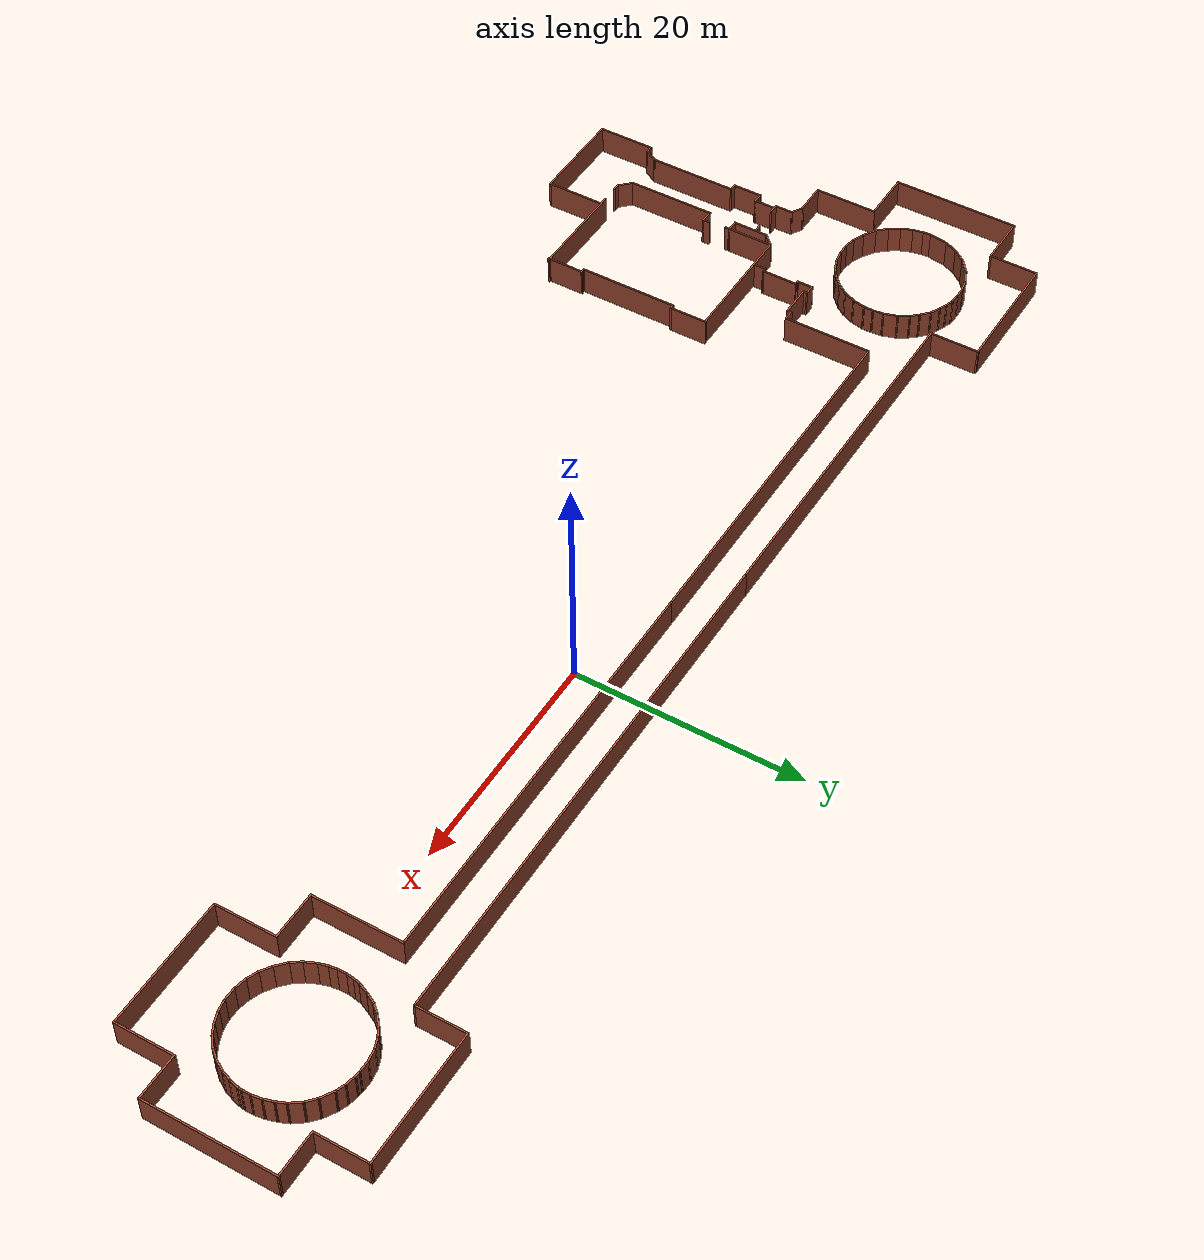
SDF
<?xml version='1.0'?>
<sdf version='1.7'>
  <model name='TD1modelado'>
    <pose>-6.73237 -9.45588 0 0 -0 0</pose>
    <link name='Wall_10'>
      <collision name='Wall_10_Collision'>
        <geometry>
          <box>
            <size>0.5 0.15 2.5</size>
          </box>
        </geometry>
        <pose>0 0 1.25 0 -0 0</pose>
      </collision>
      <visual name='Wall_10_Visual'>
        <pose>0 0 1.25 0 -0 0</pose>
        <geometry>
          <box>
            <size>0.5 0.15 2.5</size>
          </box>
        </geometry>
        <material>
          <script>
            <uri>file://media/materials/scripts/gazebo.material</uri>
            <name>Gazebo/Bricks</name>
          </script>
          <ambient>1 1 1 1</ambient>
        </material>
        <meta>
          <layer>0</layer>
        </meta>
      </visual>
      <pose>-41.4096 -4.6047 0 0 -0 1.5708</pose>
    </link>
    <link name='Wall_100'>
      <collision name='Wall_100_Collision'>
        <geometry>
          <box>
            <size>1.43544 0.15 2.5</size>
          </box>
        </geometry>
        <pose>0 0 1.25 0 -0 0</pose>
      </collision>
      <visual name='Wall_100_Visual'>
        <pose>0 0 1.25 0 -0 0</pose>
        <geometry>
          <box>
            <size>1.43544 0.15 2.5</size>
          </box>
        </geometry>
        <material>
          <script>
            <uri>file://media/materials/scripts/gazebo.material</uri>
            <name>Gazebo/Bricks</name>
          </script>
          <ambient>1 1 1 1</ambient>
        </material>
        <meta>
          <layer>0</layer>
        </meta>
      </visual>
      <pose>-49.2151 13.2258 0 0 -0 -2.00813</pose>
    </link>
    <link name='Wall_101'>
      <collision name='Wall_101_Collision'>
        <geometry>
          <box>
            <size>1.83326 0.15 2.5</size>
          </box>
        </geometry>
        <pose>0 0 1.25 0 -0 0</pose>
      </collision>
      <visual name='Wall_101_Visual'>
        <pose>0 0 1.25 0 -0 0</pose>
        <geometry>
          <box>
            <size>1.83326 0.15 2.5</size>
          </box>
        </geometry>
        <material>
          <script>
            <uri>file://media/materials/scripts/gazebo.material</uri>
            <name>Gazebo/Bricks</name>
          </script>
          <ambient>1 1 1 1</ambient>
        </material>
        <meta>
          <layer>0</layer>
        </meta>
      </visual>
      <pose>-49.6159 11.8118 0 0 -0 -1.72413</pose>
    </link>
    <link name='Wall_102'>
      <collision name='Wall_102_Collision'>
        <geometry>
          <box>
            <size>0.84713 0.15 2.5</size>
          </box>
        </geometry>
        <pose>0 0 1.25 0 -0 0</pose>
      </collision>
      <visual name='Wall_102_Visual'>
        <pose>0 0 1.25 0 -0 0</pose>
        <geometry>
          <box>
            <size>0.84713 0.15 2.5</size>
          </box>
        </geometry>
        <material>
          <script>
            <uri>file://media/materials/scripts/gazebo.material</uri>
            <name>Gazebo/Bricks</name>
          </script>
          <ambient>1 1 1 1</ambient>
        </material>
        <meta>
          <layer>0</layer>
        </meta>
      </visual>
      <pose>-49.7218 10.6322 0 0 -0 -1.50567</pose>
    </link>
    <link name='Wall_104'>
      <collision name='Wall_104_Collision'>
        <geometry>
          <box>
            <size>1.08737 0.15 2.5</size>
          </box>
        </geometry>
        <pose>0 0 1.25 0 -0 0</pose>
      </collision>
      <visual name='Wall_104_Visual'>
        <pose>0 0 1.25 0 -0 0</pose>
        <geometry>
          <box>
            <size>1.08737 0.15 2.5</size>
          </box>
        </geometry>
        <material>
          <script>
            <uri>file://media/materials/scripts/gazebo.material</uri>
            <name>Gazebo/Bricks</name>
          </script>
          <ambient>1 1 1 1</ambient>
        </material>
        <meta>
          <layer>0</layer>
        </meta>
      </visual>
      <pose>-49.6159 9.82316 0 0 -0 -1.39239</pose>
    </link>
    <link name='Wall_105'>
      <collision name='Wall_105_Collision'>
        <geometry>
          <box>
            <size>1.22277 0.15 2.5</size>
          </box>
        </geometry>
        <pose>0 0 1.25 0 -0 0</pose>
      </collision>
      <visual name='Wall_105_Visual'>
        <pose>0 0 1.25 0 -0 0</pose>
        <geometry>
          <box>
            <size>1.22277 0.15 2.5</size>
          </box>
        </geometry>
        <material>
          <script>
            <uri>file://media/materials/scripts/gazebo.material</uri>
            <name>Gazebo/Bricks</name>
          </script>
          <ambient>1 1 1 1</ambient>
        </material>
        <meta>
          <layer>0</layer>
        </meta>
      </visual>
      <pose>-49.3361 8.86286 0 0 -0 -1.19552</pose>
    </link>
    <link name='Wall_106'>
      <collision name='Wall_106_Collision'>
        <geometry>
          <box>
            <size>1.2113 0.15 2.5</size>
          </box>
        </geometry>
        <pose>0 0 1.25 0 -0 0</pose>
      </collision>
      <visual name='Wall_106_Visual'>
        <pose>0 0 1.25 0 -0 0</pose>
        <geometry>
          <box>
            <size>1.2113 0.15 2.5</size>
          </box>
        </geometry>
        <material>
          <script>
            <uri>file://media/materials/scripts/gazebo.material</uri>
            <name>Gazebo/Bricks</name>
          </script>
          <ambient>1 1 1 1</ambient>
        </material>
        <meta>
          <layer>0</layer>
        </meta>
      </visual>
      <pose>-48.8522 7.91768 0 0 -0 -0.998603</pose>
    </link>
    <link name='Wall_107'>
      <collision name='Wall_107_Collision'>
        <geometry>
          <box>
            <size>1.30569 0.15 2.5</size>
          </box>
        </geometry>
        <pose>0 0 1.25 0 -0 0</pose>
      </collision>
      <visual name='Wall_107_Visual'>
        <pose>0 0 1.25 0 -0 0</pose>
        <geometry>
          <box>
            <size>1.30569 0.15 2.5</size>
          </box>
        </geometry>
        <material>
          <script>
            <uri>file://media/materials/scripts/gazebo.material</uri>
            <name>Gazebo/Bricks</name>
          </script>
          <ambient>1 1 1 1</ambient>
        </material>
        <meta>
          <layer>0</layer>
        </meta>
      </visual>
      <pose>-48.1717 7.04812 0 0 -0 -0.822418</pose>
    </link>
    <link name='Wall_108'>
      <collision name='Wall_108_Collision'>
        <geometry>
          <box>
            <size>1.42607 0.15 2.5</size>
          </box>
        </geometry>
        <pose>0 0 1.25 0 -0 0</pose>
      </collision>
      <visual name='Wall_108_Visual'>
        <pose>0 0 1.25 0 -0 0</pose>
        <geometry>
          <box>
            <size>1.42607 0.15 2.5</size>
          </box>
        </geometry>
        <material>
          <script>
            <uri>file://media/materials/scripts/gazebo.material</uri>
            <name>Gazebo/Bricks</name>
          </script>
          <ambient>1 1 1 1</ambient>
        </material>
        <meta>
          <layer>0</layer>
        </meta>
      </visual>
      <pose>-47.234 6.29197 0 0 -0 -0.548549</pose>
    </link>
    <link name='Wall_109'>
      <collision name='Wall_109_Collision'>
        <geometry>
          <box>
            <size>1.24815 0.15 2.5</size>
          </box>
        </geometry>
        <pose>0 0 1.25 0 -0 0</pose>
      </collision>
      <visual name='Wall_109_Visual'>
        <pose>0 0 1.25 0 -0 0</pose>
        <geometry>
          <box>
            <size>1.24815 0.15 2.5</size>
          </box>
        </geometry>
        <material>
          <script>
            <uri>file://media/materials/scripts/gazebo.material</uri>
            <name>Gazebo/Bricks</name>
          </script>
          <ambient>1 1 1 1</ambient>
        </material>
        <meta>
          <layer>0</layer>
        </meta>
      </visual>
      <pose>-46.183 5.74755 0 0 -0 -0.39585</pose>
    </link>
    <link name='Wall_110'>
      <collision name='Wall_110_Collision'>
        <geometry>
          <box>
            <size>1.21184 0.15 2.5</size>
          </box>
        </geometry>
        <pose>0 0 1.25 0 -0 0</pose>
      </collision>
      <visual name='Wall_110_Visual'>
        <pose>0 0 1.25 0 -0 0</pose>
        <geometry>
          <box>
            <size>1.21184 0.15 2.5</size>
          </box>
        </geometry>
        <material>
          <script>
            <uri>file://media/materials/scripts/gazebo.material</uri>
            <name>Gazebo/Bricks</name>
          </script>
          <ambient>1 1 1 1</ambient>
        </material>
        <meta>
          <layer>0</layer>
        </meta>
      </visual>
      <pose>-45.1546 5.43753 0 0 -0 -0.186223</pose>
    </link>
    <link name='Wall_111'>
      <collision name='Wall_111_Collision'>
        <geometry>
          <box>
            <size>1.14857 0.15 2.5</size>
          </box>
        </geometry>
        <pose>0 0 1.25 0 -0 0</pose>
      </collision>
      <visual name='Wall_111_Visual'>
        <pose>0 0 1.25 0 -0 0</pose>
        <geometry>
          <box>
            <size>1.14857 0.15 2.5</size>
          </box>
        </geometry>
        <material>
          <script>
            <uri>file://media/materials/scripts/gazebo.material</uri>
            <name>Gazebo/Bricks</name>
          </script>
          <ambient>1 1 1 1</ambient>
        </material>
        <meta>
          <layer>0</layer>
        </meta>
      </visual>
      <pose>-44.1338 5.35435 0 0 -0 0.030294</pose>
    </link>
    <link name='Wall_112'>
      <collision name='Wall_112_Collision'>
        <geometry>
          <box>
            <size>1.26643 0.15 2.5</size>
          </box>
        </geometry>
        <pose>0 0 1.25 0 -0 0</pose>
      </collision>
      <visual name='Wall_112_Visual'>
        <pose>0 0 1.25 0 -0 0</pose>
        <geometry>
          <box>
            <size>1.26643 0.15 2.5</size>
          </box>
        </geometry>
        <material>
          <script>
            <uri>file://media/materials/scripts/gazebo.material</uri>
            <name>Gazebo/Bricks</name>
          </script>
          <ambient>1 1 1 1</ambient>
        </material>
        <meta>
          <layer>0</layer>
        </meta>
      </visual>
      <pose>-43.0828 5.45265 0 0 -0 0.14956</pose>
    </link>
    <link name='Wall_113'>
      <collision name='Wall_113_Collision'>
        <geometry>
          <box>
            <size>1.1528 0.15 2.5</size>
          </box>
        </geometry>
        <pose>0 0 1.25 0 -0 0</pose>
      </collision>
      <visual name='Wall_113_Visual'>
        <pose>0 0 1.25 0 -0 0</pose>
        <geometry>
          <box>
            <size>1.1528 0.15 2.5</size>
          </box>
        </geometry>
        <material>
          <script>
            <uri>file://media/materials/scripts/gazebo.material</uri>
            <name>Gazebo/Bricks</name>
          </script>
          <ambient>1 1 1 1</ambient>
        </material>
        <meta>
          <layer>0</layer>
        </meta>
      </visual>
      <pose>-42.0696 5.73243 0 0 -0 0.402912</pose>
    </link>
    <link name='Wall_114'>
      <collision name='Wall_114_Collision'>
        <geometry>
          <box>
            <size>1.1904 0.15 2.5</size>
          </box>
        </geometry>
        <pose>0 0 1.25 0 -0 0</pose>
      </collision>
      <visual name='Wall_114_Visual'>
        <pose>0 0 1.25 0 -0 0</pose>
        <geometry>
          <box>
            <size>1.1904 0.15 2.5</size>
          </box>
        </geometry>
        <material>
          <script>
            <uri>file://media/materials/scripts/gazebo.material</uri>
            <name>Gazebo/Bricks</name>
          </script>
          <ambient>1 1 1 1</ambient>
        </material>
        <meta>
          <layer>0</layer>
        </meta>
      </visual>
      <pose>-41.1698 6.2088 0 0 -0 0.567844</pose>
    </link>
    <link name='Wall_115'>
      <collision name='Wall_115_Collision'>
        <geometry>
          <box>
            <size>1.32648 0.15 2.5</size>
          </box>
        </geometry>
        <pose>0 0 1.25 0 -0 0</pose>
      </collision>
      <visual name='Wall_115_Visual'>
        <pose>0 0 1.25 0 -0 0</pose>
        <geometry>
          <box>
            <size>1.32648 0.15 2.5</size>
          </box>
        </geometry>
        <material>
          <script>
            <uri>file://media/materials/scripts/gazebo.material</uri>
            <name>Gazebo/Bricks</name>
          </script>
          <ambient>1 1 1 1</ambient>
        </material>
        <meta>
          <layer>0</layer>
        </meta>
      </visual>
      <pose>-40.3078 6.89689 0 0 -0 0.767218</pose>
    </link>
    <link name='Wall_116'>
      <collision name='Wall_116_Collision'>
        <geometry>
          <box>
            <size>1.20308 0.15 2.5</size>
          </box>
        </geometry>
        <pose>0 0 1.25 0 -0 0</pose>
      </collision>
      <visual name='Wall_116_Visual'>
        <pose>0 0 1.25 0 -0 0</pose>
        <geometry>
          <box>
            <size>1.20308 0.15 2.5</size>
          </box>
        </geometry>
        <material>
          <script>
            <uri>file://media/materials/scripts/gazebo.material</uri>
            <name>Gazebo/Bricks</name>
          </script>
          <ambient>1 1 1 1</ambient>
        </material>
        <meta>
          <layer>0</layer>
        </meta>
      </visual>
      <pose>-39.5819 7.73621 0 0 -0 0.958894</pose>
    </link>
    <link name='Wall_117'>
      <collision name='Wall_117_Collision'>
        <geometry>
          <box>
            <size>1.28189 0.15 2.5</size>
          </box>
        </geometry>
        <pose>0 0 1.25 0 -0 0</pose>
      </collision>
      <visual name='Wall_117_Visual'>
        <pose>0 0 1.25 0 -0 0</pose>
        <geometry>
          <box>
            <size>1.28189 0.15 2.5</size>
          </box>
        </geometry>
        <material>
          <script>
            <uri>file://media/materials/scripts/gazebo.material</uri>
            <name>Gazebo/Bricks</name>
          </script>
          <ambient>1 1 1 1</ambient>
        </material>
        <meta>
          <layer>0</layer>
        </meta>
      </visual>
      <pose>-39.0601 8.68895 0 0 -0 1.17292</pose>
    </link>
    <link name='Wall_118'>
      <collision name='Wall_118_Collision'>
        <geometry>
          <box>
            <size>1.28018 0.15 2.5</size>
          </box>
        </geometry>
        <pose>0 0 1.25 0 -0 0</pose>
      </collision>
      <visual name='Wall_118_Visual'>
        <pose>0 0 1.25 0 -0 0</pose>
        <geometry>
          <box>
            <size>1.28018 0.15 2.5</size>
          </box>
        </geometry>
        <material>
          <script>
            <uri>file://media/materials/scripts/gazebo.material</uri>
            <name>Gazebo/Bricks</name>
          </script>
          <ambient>1 1 1 1</ambient>
        </material>
        <meta>
          <layer>0</layer>
        </meta>
      </visual>
      <pose>-38.7199 9.76267 0 0 -0 1.35503</pose>
    </link>
    <link name='Wall_120'>
      <collision name='Wall_120_Collision'>
        <geometry>
          <box>
            <size>1 0.15 2.5</size>
          </box>
        </geometry>
        <pose>0 0 1.25 0 -0 0</pose>
      </collision>
      <visual name='Wall_120_Visual'>
        <pose>0 0 1.25 0 -0 0</pose>
        <geometry>
          <box>
            <size>1 0.15 2.5</size>
          </box>
        </geometry>
        <material>
          <script>
            <uri>file://media/materials/scripts/gazebo.material</uri>
            <name>Gazebo/Bricks</name>
          </script>
          <ambient>1 1 1 1</ambient>
        </material>
        <meta>
          <layer>0</layer>
        </meta>
      </visual>
      <pose>-38.5989 10.7397 0 0 -0 1.5708</pose>
    </link>
    <link name='Wall_121'>
      <collision name='Wall_121_Collision'>
        <geometry>
          <box>
            <size>1.08755 0.15 2.5</size>
          </box>
        </geometry>
        <pose>0 0 1.25 0 -0 0</pose>
      </collision>
      <visual name='Wall_121_Visual'>
        <pose>0 0 1.25 0 -0 0</pose>
        <geometry>
          <box>
            <size>1.08755 0.15 2.5</size>
          </box>
        </geometry>
        <material>
          <script>
            <uri>file://media/materials/scripts/gazebo.material</uri>
            <name>Gazebo/Bricks</name>
          </script>
          <ambient>1 1 1 1</ambient>
        </material>
        <meta>
          <layer>0</layer>
        </meta>
      </visual>
      <pose>-38.6367 11.6319 0 0 -0 1.65153</pose>
    </link>
    <link name='Wall_122'>
      <collision name='Wall_122_Collision'>
        <geometry>
          <box>
            <size>1.37905 0.15 2.5</size>
          </box>
        </geometry>
        <pose>0 0 1.25 0 -0 0</pose>
      </collision>
      <visual name='Wall_122_Visual'>
        <pose>0 0 1.25 0 -0 0</pose>
        <geometry>
          <box>
            <size>1.37905 0.15 2.5</size>
          </box>
        </geometry>
        <material>
          <script>
            <uri>file://media/materials/scripts/gazebo.material</uri>
            <name>Gazebo/Bricks</name>
          </script>
          <ambient>1 1 1 1</ambient>
        </material>
        <meta>
          <layer>0</layer>
        </meta>
      </visual>
      <pose>-38.8711 12.6814 0 0 -0 1.89644</pose>
    </link>
    <link name='Wall_123'>
      <collision name='Wall_123_Collision'>
        <geometry>
          <box>
            <size>1.16673 0.15 2.5</size>
          </box>
        </geometry>
        <pose>0 0 1.25 0 -0 0</pose>
      </collision>
      <visual name='Wall_123_Visual'>
        <pose>0 0 1.25 0 -0 0</pose>
        <geometry>
          <box>
            <size>1.16673 0.15 2.5</size>
          </box>
        </geometry>
        <material>
          <script>
            <uri>file://media/materials/scripts/gazebo.material</uri>
            <name>Gazebo/Bricks</name>
          </script>
          <ambient>1 1 1 1</ambient>
        </material>
        <meta>
          <layer>0</layer>
        </meta>
      </visual>
      <pose>-39.3248 13.7022 0 0 -0 2.10101</pose>
    </link>
    <link name='Wall_124'>
      <collision name='Wall_124_Collision'>
        <geometry>
          <box>
            <size>0.986556 0.15 2.5</size>
          </box>
        </geometry>
        <pose>0 0 1.25 0 -0 0</pose>
      </collision>
      <visual name='Wall_124_Visual'>
        <pose>0 0 1.25 0 -0 0</pose>
        <geometry>
          <box>
            <size>0.986556 0.15 2.5</size>
          </box>
        </geometry>
        <material>
          <script>
            <uri>file://media/materials/scripts/gazebo.material</uri>
            <name>Gazebo/Bricks</name>
          </script>
          <ambient>1 1 1 1</ambient>
        </material>
        <meta>
          <layer>0</layer>
        </meta>
      </visual>
      <pose>-39.8541 14.4583 0 0 -0 2.27942</pose>
    </link>
    <link name='Wall_125'>
      <collision name='Wall_125_Collision'>
        <geometry>
          <box>
            <size>1.14501 0.15 2.5</size>
          </box>
        </geometry>
        <pose>0 0 1.25 0 -0 0</pose>
      </collision>
      <visual name='Wall_125_Visual'>
        <pose>0 0 1.25 0 -0 0</pose>
        <geometry>
          <box>
            <size>1.14501 0.15 2.5</size>
          </box>
        </geometry>
        <material>
          <script>
            <uri>file://media/materials/scripts/gazebo.material</uri>
            <name>Gazebo/Bricks</name>
          </script>
          <ambient>1 1 1 1</ambient>
        </material>
        <meta>
          <layer>0</layer>
        </meta>
      </visual>
      <pose>-40.4892 15.1162 0 0 -0 2.38844</pose>
    </link>
    <link name='Wall_126'>
      <collision name='Wall_126_Collision'>
        <geometry>
          <box>
            <size>1.04315 0.15 2.5</size>
          </box>
        </geometry>
        <pose>0 0 1.25 0 -0 0</pose>
      </collision>
      <visual name='Wall_126_Visual'>
        <pose>0 0 1.25 0 -0 0</pose>
        <geometry>
          <box>
            <size>1.04315 0.15 2.5</size>
          </box>
        </geometry>
        <material>
          <script>
            <uri>file://media/materials/scripts/gazebo.material</uri>
            <name>Gazebo/Bricks</name>
          </script>
          <ambient>1 1 1 1</ambient>
        </material>
        <meta>
          <layer>0</layer>
        </meta>
      </visual>
      <pose>-41.2454 15.6682 0 0 -0 2.64765</pose>
    </link>
    <link name='Wall_127'>
      <collision name='Wall_127_Collision'>
        <geometry>
          <box>
            <size>0.874794 0.15 2.5</size>
          </box>
        </geometry>
        <pose>0 0 1.25 0 -0 0</pose>
      </collision>
      <visual name='Wall_127_Visual'>
        <pose>0 0 1.25 0 -0 0</pose>
        <geometry>
          <box>
            <size>0.874794 0.15 2.5</size>
          </box>
        </geometry>
        <material>
          <script>
            <uri>file://media/materials/scripts/gazebo.material</uri>
            <name>Gazebo/Bricks</name>
          </script>
          <ambient>1 1 1 1</ambient>
        </material>
        <meta>
          <layer>0</layer>
        </meta>
      </visual>
      <pose>-41.9713 16.0235 0 0 -0 2.73396</pose>
    </link>
    <link name='Wall_128'>
      <collision name='Wall_128_Collision'>
        <geometry>
          <box>
            <size>0.881703 0.15 2.5</size>
          </box>
        </geometry>
        <pose>0 0 1.25 0 -0 0</pose>
      </collision>
      <visual name='Wall_128_Visual'>
        <pose>0 0 1.25 0 -0 0</pose>
        <geometry>
          <box>
            <size>0.881703 0.15 2.5</size>
          </box>
        </geometry>
        <material>
          <script>
            <uri>file://media/materials/scripts/gazebo.material</uri>
            <name>Gazebo/Bricks</name>
          </script>
          <ambient>1 1 1 1</ambient>
        </material>
        <meta>
          <layer>0</layer>
        </meta>
      </visual>
      <pose>-42.6518 16.2806 0 0 -0 2.82638</pose>
    </link>
    <link name='Wall_129'>
      <collision name='Wall_129_Collision'>
        <geometry>
          <box>
            <size>0.971661 0.15 2.5</size>
          </box>
        </geometry>
        <pose>0 0 1.25 0 -0 0</pose>
      </collision>
      <visual name='Wall_129_Visual'>
        <pose>0 0 1.25 0 -0 0</pose>
        <geometry>
          <box>
            <size>0.971661 0.15 2.5</size>
          </box>
        </geometry>
        <material>
          <script>
            <uri>file://media/materials/scripts/gazebo.material</uri>
            <name>Gazebo/Bricks</name>
          </script>
          <ambient>1 1 1 1</ambient>
        </material>
        <meta>
          <layer>0</layer>
        </meta>
      </visual>
      <pose>-43.4079 16.4394 0 0 -0 3.03093</pose>
    </link>
    <link name='Wall_130'>
      <collision name='Wall_130_Collision'>
        <geometry>
          <box>
            <size>1.07249 0.15 2.5</size>
          </box>
        </geometry>
        <pose>0 0 1.25 0 -0 0</pose>
      </collision>
      <visual name='Wall_130_Visual'>
        <pose>0 0 1.25 0 -0 0</pose>
        <geometry>
          <box>
            <size>1.07249 0.15 2.5</size>
          </box>
        </geometry>
        <material>
          <script>
            <uri>file://media/materials/scripts/gazebo.material</uri>
            <name>Gazebo/Bricks</name>
          </script>
          <ambient>1 1 1 1</ambient>
        </material>
        <meta>
          <layer>0</layer>
        </meta>
      </visual>
      <pose>-44.2775 16.4772 0 0 -0 -3.1252</pose>
    </link>
    <link name='Wall_131'>
      <collision name='Wall_131_Collision'>
        <geometry>
          <box>
            <size>1.16447 0.15 2.5</size>
          </box>
        </geometry>
        <pose>0 0 1.25 0 -0 0</pose>
      </collision>
      <visual name='Wall_131_Visual'>
        <pose>0 0 1.25 0 -0 0</pose>
        <geometry>
          <box>
            <size>1.16447 0.15 2.5</size>
          </box>
        </geometry>
        <material>
          <script>
            <uri>file://media/materials/scripts/gazebo.material</uri>
            <name>Gazebo/Bricks</name>
          </script>
          <ambient>1 1 1 1</ambient>
        </material>
        <meta>
          <layer>0</layer>
        </meta>
      </visual>
      <pose>-45.2378 16.3789 0 0 -0 -2.96174</pose>
    </link>
    <link name='Wall_133'>
      <collision name='Wall_133_Collision'>
        <geometry>
          <box>
            <size>0.936535 0.15 2.5</size>
          </box>
        </geometry>
        <pose>0 0 1.25 0 -0 0</pose>
      </collision>
      <visual name='Wall_133_Visual'>
        <pose>0 0 1.25 0 -0 0</pose>
        <geometry>
          <box>
            <size>0.936535 0.15 2.5</size>
          </box>
        </geometry>
        <material>
          <script>
            <uri>file://media/materials/scripts/gazebo.material</uri>
            <name>Gazebo/Bricks</name>
          </script>
          <ambient>1 1 1 1</ambient>
        </material>
        <meta>
          <layer>0</layer>
        </meta>
      </visual>
      <pose>39.3862 10.8872 0 0 -0 -1.55157</pose>
    </link>
    <link name='Wall_134'>
      <collision name='Wall_134_Collision'>
        <geometry>
          <box>
            <size>0.836552 0.15 2.5</size>
          </box>
        </geometry>
        <pose>0 0 1.25 0 -0 0</pose>
      </collision>
      <visual name='Wall_134_Visual'>
        <pose>0 0 1.25 0 -0 0</pose>
        <geometry>
          <box>
            <size>0.836552 0.15 2.5</size>
          </box>
        </geometry>
        <material>
          <script>
            <uri>file://media/materials/scripts/gazebo.material</uri>
            <name>Gazebo/Bricks</name>
          </script>
          <ambient>1 1 1 1</ambient>
        </material>
        <meta>
          <layer>0</layer>
        </meta>
      </visual>
      <pose>39.4392 10.1538 0 0 -0 -1.43824</pose>
    </link>
    <link name='Wall_135'>
      <collision name='Wall_135_Collision'>
        <geometry>
          <box>
            <size>0.949798 0.15 2.5</size>
          </box>
        </geometry>
        <pose>0 0 1.25 0 -0 0</pose>
      </collision>
      <visual name='Wall_135_Visual'>
        <pose>0 0 1.25 0 -0 0</pose>
        <geometry>
          <box>
            <size>0.949798 0.15 2.5</size>
          </box>
        </geometry>
        <material>
          <script>
            <uri>file://media/materials/scripts/gazebo.material</uri>
            <name>Gazebo/Bricks</name>
          </script>
          <ambient>1 1 1 1</ambient>
        </material>
        <meta>
          <layer>0</layer>
        </meta>
      </visual>
      <pose>39.5904 9.42789 0 0 -0 -1.30289</pose>
    </link>
    <link name='Wall_136'>
      <collision name='Wall_136_Collision'>
        <geometry>
          <box>
            <size>1.1788 0.15 2.5</size>
          </box>
        </geometry>
        <pose>0 0 1.25 0 -0 0</pose>
      </collision>
      <visual name='Wall_136_Visual'>
        <pose>0 0 1.25 0 -0 0</pose>
        <geometry>
          <box>
            <size>1.1788 0.15 2.5</size>
          </box>
        </geometry>
        <material>
          <script>
            <uri>file://media/materials/scripts/gazebo.material</uri>
            <name>Gazebo/Bricks</name>
          </script>
          <ambient>1 1 1 1</ambient>
        </material>
        <meta>
          <layer>0</layer>
        </meta>
      </visual>
      <pose>39.908 8.57345 0 0 -0 -1.1466</pose>
    </link>
    <link name='Wall_137'>
      <collision name='Wall_137_Collision'>
        <geometry>
          <box>
            <size>1.08542 0.15 2.5</size>
          </box>
        </geometry>
        <pose>0 0 1.25 0 -0 0</pose>
      </collision>
      <visual name='Wall_137_Visual'>
        <pose>0 0 1.25 0 -0 0</pose>
        <geometry>
          <box>
            <size>1.08542 0.15 2.5</size>
          </box>
        </geometry>
        <material>
          <script>
            <uri>file://media/materials/scripts/gazebo.material</uri>
            <name>Gazebo/Bricks</name>
          </script>
          <ambient>1 1 1 1</ambient>
        </material>
        <meta>
          <layer>0</layer>
        </meta>
      </visual>
      <pose>40.3843 7.71901 0 0 -0 -0.969342</pose>
    </link>
    <link name='Wall_138'>
      <collision name='Wall_138_Collision'>
        <geometry>
          <box>
            <size>1.28432 0.15 2.5</size>
          </box>
        </geometry>
        <pose>0 0 1.25 0 -0 0</pose>
      </collision>
      <visual name='Wall_138_Visual'>
        <pose>0 0 1.25 0 -0 0</pose>
        <geometry>
          <box>
            <size>1.28432 0.15 2.5</size>
          </box>
        </geometry>
        <material>
          <script>
            <uri>file://media/materials/scripts/gazebo.material</uri>
            <name>Gazebo/Bricks</name>
          </script>
          <ambient>1 1 1 1</ambient>
        </material>
        <meta>
          <layer>0</layer>
        </meta>
      </visual>
      <pose>41.0649 6.94774 0 0 -0 -0.74768</pose>
    </link>
    <link name='Wall_139'>
      <collision name='Wall_139_Collision'>
        <geometry>
          <box>
            <size>1.19446 0.15 2.5</size>
          </box>
        </geometry>
        <pose>0 0 1.25 0 -0 0</pose>
      </collision>
      <visual name='Wall_139_Visual'>
        <pose>0 0 1.25 0 -0 0</pose>
        <geometry>
          <box>
            <size>1.19446 0.15 2.5</size>
          </box>
        </geometry>
        <material>
          <script>
            <uri>file://media/materials/scripts/gazebo.material</uri>
            <name>Gazebo/Bricks</name>
          </script>
          <ambient>1 1 1 1</ambient>
        </material>
        <meta>
          <layer>0</layer>
        </meta>
      </visual>
      <pose>41.9118 6.26721 0 0 -0 -0.60005</pose>
    </link>
    <link name='Wall_14'>
      <collision name='Wall_14_Collision'>
        <geometry>
          <box>
            <size>0.15 0.15 2.5</size>
          </box>
        </geometry>
        <pose>0 0 1.25 0 -0 0</pose>
      </collision>
      <visual name='Wall_14_Visual'>
        <pose>0 0 1.25 0 -0 0</pose>
        <geometry>
          <box>
            <size>0.15 0.15 2.5</size>
          </box>
        </geometry>
        <material>
          <script>
            <uri>file://media/materials/scripts/gazebo.material</uri>
            <name>Gazebo/Grey</name>
          </script>
          <ambient>1 1 1 1</ambient>
        </material>
        <meta>
          <layer>0</layer>
        </meta>
      </visual>
      <pose>-43.0807 -2.35971 0 0 -0 0</pose>
    </link>
    <link name='Wall_140'>
      <collision name='Wall_140_Collision'>
        <geometry>
          <box>
            <size>1.18069 0.15 2.5</size>
          </box>
        </geometry>
        <pose>0 0 1.25 0 -0 0</pose>
      </collision>
      <visual name='Wall_140_Visual'>
        <pose>0 0 1.25 0 -0 0</pose>
        <geometry>
          <box>
            <size>1.18069 0.15 2.5</size>
          </box>
        </geometry>
        <material>
          <script>
            <uri>file://media/materials/scripts/gazebo.material</uri>
            <name>Gazebo/Bricks</name>
          </script>
          <ambient>1 1 1 1</ambient>
        </material>
        <meta>
          <layer>0</layer>
        </meta>
      </visual>
      <pose>42.8191 5.77572 0 0 -0 -0.391405</pose>
    </link>
    <link name='Wall_141'>
      <collision name='Wall_141_Collision'>
        <geometry>
          <box>
            <size>1.21785 0.15 2.5</size>
          </box>
        </geometry>
        <pose>0 0 1.25 0 -0 0</pose>
      </collision>
      <visual name='Wall_141_Visual'>
        <pose>0 0 1.25 0 -0 0</pose>
        <geometry>
          <box>
            <size>1.21785 0.15 2.5</size>
          </box>
        </geometry>
        <material>
          <script>
            <uri>file://media/materials/scripts/gazebo.material</uri>
            <name>Gazebo/Bricks</name>
          </script>
          <ambient>1 1 1 1</ambient>
        </material>
        <meta>
          <layer>0</layer>
        </meta>
      </visual>
      <pose>43.8172 5.4657 0 0 -0 -0.214061</pose>
    </link>
    <link name='Wall_142'>
      <collision name='Wall_142_Collision'>
        <geometry>
          <box>
            <size>1.22383 0.15 2.5</size>
          </box>
        </geometry>
        <pose>0 0 1.25 0 -0 0</pose>
      </collision>
      <visual name='Wall_142_Visual'>
        <pose>0 0 1.25 0 -0 0</pose>
        <geometry>
          <box>
            <size>1.22383 0.15 2.5</size>
          </box>
        </geometry>
        <material>
          <script>
            <uri>file://media/materials/scripts/gazebo.material</uri>
            <name>Gazebo/Bricks</name>
          </script>
          <ambient>1 1 1 1</ambient>
        </material>
        <meta>
          <layer>0</layer>
        </meta>
      </visual>
      <pose>44.8758 5.34471 0 0 -0 -0.014084</pose>
    </link>
    <link name='Wall_143'>
      <collision name='Wall_143_Collision'>
        <geometry>
          <box>
            <size>1.06989 0.15 2.5</size>
          </box>
        </geometry>
        <pose>0 0 1.25 0 -0 0</pose>
      </collision>
      <visual name='Wall_143_Visual'>
        <pose>0 0 1.25 0 -0 0</pose>
        <geometry>
          <box>
            <size>1.06989 0.15 2.5</size>
          </box>
        </geometry>
        <material>
          <script>
            <uri>file://media/materials/scripts/gazebo.material</uri>
            <name>Gazebo/Bricks</name>
          </script>
          <ambient>1 1 1 1</ambient>
        </material>
        <meta>
          <layer>0</layer>
        </meta>
      </visual>
      <pose>45.8664 5.41277 0 0 -0 0.165149</pose>
    </link>
    <link name='Wall_144'>
      <collision name='Wall_144_Collision'>
        <geometry>
          <box>
            <size>1.19785 0.15 2.5</size>
          </box>
        </geometry>
        <pose>0 0 1.25 0 -0 0</pose>
      </collision>
      <visual name='Wall_144_Visual'>
        <pose>0 0 1.25 0 -0 0</pose>
        <geometry>
          <box>
            <size>1.19785 0.15 2.5</size>
          </box>
        </geometry>
        <material>
          <script>
            <uri>file://media/materials/scripts/gazebo.material</uri>
            <name>Gazebo/Bricks</name>
          </script>
          <ambient>1 1 1 1</ambient>
        </material>
        <meta>
          <layer>0</layer>
        </meta>
      </visual>
      <pose>46.8116 5.66986 0 0 -0 0.353703</pose>
    </link>
    <link name='Wall_145'>
      <collision name='Wall_145_Collision'>
        <geometry>
          <box>
            <size>1.04315 0.15 2.5</size>
          </box>
        </geometry>
        <pose>0 0 1.25 0 -0 0</pose>
      </collision>
      <visual name='Wall_145_Visual'>
        <pose>0 0 1.25 0 -0 0</pose>
        <geometry>
          <box>
            <size>1.04315 0.15 2.5</size>
          </box>
        </geometry>
        <material>
          <script>
            <uri>file://media/materials/scripts/gazebo.material</uri>
            <name>Gazebo/Bricks</name>
          </script>
          <ambient>1 1 1 1</ambient>
        </material>
        <meta>
          <layer>0</layer>
        </meta>
      </visual>
      <pose>47.6963 6.06305 0 0 -0 0.493941</pose>
    </link>
    <link name='Wall_146'>
      <collision name='Wall_146_Collision'>
        <geometry>
          <box>
            <size>1.17043 0.15 2.5</size>
          </box>
        </geometry>
        <pose>0 0 1.25 0 -0 0</pose>
      </collision>
      <visual name='Wall_146_Visual'>
        <pose>0 0 1.25 0 -0 0</pose>
        <geometry>
          <box>
            <size>1.17043 0.15 2.5</size>
          </box>
        </geometry>
        <material>
          <script>
            <uri>file://media/materials/scripts/gazebo.material</uri>
            <name>Gazebo/Bricks</name>
          </script>
          <ambient>1 1 1 1</ambient>
        </material>
        <meta>
          <layer>0</layer>
        </meta>
      </visual>
      <pose>48.4826 6.59991 0 0 -0 0.690943</pose>
    </link>
    <link name='Wall_147'>
      <collision name='Wall_147_Collision'>
        <geometry>
          <box>
            <size>1.19172 0.15 2.5</size>
          </box>
        </geometry>
        <pose>0 0 1.25 0 -0 0</pose>
      </collision>
      <visual name='Wall_147_Visual'>
        <pose>0 0 1.25 0 -0 0</pose>
        <geometry>
          <box>
            <size>1.19172 0.15 2.5</size>
          </box>
        </geometry>
        <material>
          <script>
            <uri>file://media/materials/scripts/gazebo.material</uri>
            <name>Gazebo/Bricks</name>
          </script>
          <ambient>1 1 1 1</ambient>
        </material>
        <meta>
          <layer>0</layer>
        </meta>
      </visual>
      <pose>49.2085 7.32581 0 0 -0 0.877917</pose>
    </link>
    <link name='Wall_148'>
      <collision name='Wall_148_Collision'>
        <geometry>
          <box>
            <size>1.17233 0.15 2.5</size>
          </box>
        </geometry>
        <pose>0 0 1.25 0 -0 0</pose>
      </collision>
      <visual name='Wall_148_Visual'>
        <pose>0 0 1.25 0 -0 0</pose>
        <geometry>
          <box>
            <size>1.17233 0.15 2.5</size>
          </box>
        </geometry>
        <material>
          <script>
            <uri>file://media/materials/scripts/gazebo.material</uri>
            <name>Gazebo/Bricks</name>
          </script>
          <ambient>1 1 1 1</ambient>
        </material>
        <meta>
          <layer>0</layer>
        </meta>
      </visual>
      <pose>49.7908 8.17269 0 0 -0 1.06082</pose>
    </link>
    <link name='Wall_149'>
      <collision name='Wall_149_Collision'>
        <geometry>
          <box>
            <size>0.98217 0.15 2.5</size>
          </box>
        </geometry>
        <pose>0 0 1.25 0 -0 0</pose>
      </collision>
      <visual name='Wall_149_Visual'>
        <pose>0 0 1.25 0 -0 0</pose>
        <geometry>
          <box>
            <size>0.98217 0.15 2.5</size>
          </box>
        </geometry>
        <material>
          <script>
            <uri>file://media/materials/scripts/gazebo.material</uri>
            <name>Gazebo/Bricks</name>
          </script>
          <ambient>1 1 1 1</ambient>
        </material>
        <meta>
          <layer>0</layer>
        </meta>
      </visual>
      <pose>50.1764 9.01201 0 0 -0 1.23755</pose>
    </link>
    <link name='Wall_150'>
      <collision name='Wall_150_Collision'>
        <geometry>
          <box>
            <size>0.960592 0.15 2.5</size>
          </box>
        </geometry>
        <pose>0 0 1.25 0 -0 0</pose>
      </collision>
      <visual name='Wall_150_Visual'>
        <pose>0 0 1.25 0 -0 0</pose>
        <geometry>
          <box>
            <size>0.960592 0.15 2.5</size>
          </box>
        </geometry>
        <material>
          <script>
            <uri>file://media/materials/scripts/gazebo.material</uri>
            <name>Gazebo/Bricks</name>
          </script>
          <ambient>1 1 1 1</ambient>
        </material>
        <meta>
          <layer>0</layer>
        </meta>
      </visual>
      <pose>50.4108 9.7984 0 0 -0 1.32582</pose>
    </link>
    <link name='Wall_151'>
      <collision name='Wall_151_Collision'>
        <geometry>
          <box>
            <size>0.499139 0.15 2.5</size>
          </box>
        </geometry>
        <pose>0 0 1.25 0 -0 0</pose>
      </collision>
      <visual name='Wall_151_Visual'>
        <pose>0 0 1.25 0 -0 0</pose>
        <geometry>
          <box>
            <size>0.499139 0.15 2.5</size>
          </box>
        </geometry>
        <material>
          <script>
            <uri>file://media/materials/scripts/gazebo.material</uri>
            <name>Gazebo/Bricks</name>
          </script>
          <ambient>1 1 1 1</ambient>
        </material>
        <meta>
          <layer>0</layer>
        </meta>
      </visual>
      <pose>50.5242 10.3655 0 0 -0 1.48406</pose>
    </link>
    <link name='Wall_152'>
      <collision name='Wall_152_Collision'>
        <geometry>
          <box>
            <size>0.891175 0.15 2.5</size>
          </box>
        </geometry>
        <pose>0 0 1.25 0 -0 0</pose>
      </collision>
      <visual name='Wall_152_Visual'>
        <pose>0 0 1.25 0 -0 0</pose>
        <geometry>
          <box>
            <size>0.891175 0.15 2.5</size>
          </box>
        </geometry>
        <material>
          <script>
            <uri>file://media/materials/scripts/gazebo.material</uri>
            <name>Gazebo/Bricks</name>
          </script>
          <ambient>1 1 1 1</ambient>
        </material>
        <meta>
          <layer>0</layer>
        </meta>
      </visual>
      <pose>50.5318 10.9099 0 0 -0 1.5912</pose>
    </link>
    <link name='Wall_154'>
      <collision name='Wall_154_Collision'>
        <geometry>
          <box>
            <size>1.00775 0.15 2.5</size>
          </box>
        </geometry>
        <pose>0 0 1.25 0 -0 0</pose>
      </collision>
      <visual name='Wall_154_Visual'>
        <pose>0 0 1.25 0 -0 0</pose>
        <geometry>
          <box>
            <size>1.00775 0.15 2.5</size>
          </box>
        </geometry>
        <material>
          <script>
            <uri>file://media/materials/scripts/gazebo.material</uri>
            <name>Gazebo/Bricks</name>
          </script>
          <ambient>1 1 1 1</ambient>
        </material>
        <meta>
          <layer>0</layer>
        </meta>
      </visual>
      <pose>50.4562 11.7039 0 0 -0 1.73015</pose>
    </link>
    <link name='Wall_155'>
      <collision name='Wall_155_Collision'>
        <geometry>
          <box>
            <size>1.02058 0.15 2.5</size>
          </box>
        </geometry>
        <pose>0 0 1.25 0 -0 0</pose>
      </collision>
      <visual name='Wall_155_Visual'>
        <pose>0 0 1.25 0 -0 0</pose>
        <geometry>
          <box>
            <size>1.02058 0.15 2.5</size>
          </box>
        </geometry>
        <material>
          <script>
            <uri>file://media/materials/scripts/gazebo.material</uri>
            <name>Gazebo/Bricks</name>
          </script>
          <ambient>1 1 1 1</ambient>
        </material>
        <meta>
          <layer>0</layer>
        </meta>
      </visual>
      <pose>50.2596 12.5432 0 0 -0 1.87057</pose>
    </link>
    <link name='Wall_156'>
      <collision name='Wall_156_Collision'>
        <geometry>
          <box>
            <size>0.970128 0.15 2.5</size>
          </box>
        </geometry>
        <pose>0 0 1.25 0 -0 0</pose>
      </collision>
      <visual name='Wall_156_Visual'>
        <pose>0 0 1.25 0 -0 0</pose>
        <geometry>
          <box>
            <size>0.970128 0.15 2.5</size>
          </box>
        </geometry>
        <material>
          <script>
            <uri>file://media/materials/scripts/gazebo.material</uri>
            <name>Gazebo/Bricks</name>
          </script>
          <ambient>1 1 1 1</ambient>
        </material>
        <meta>
          <layer>0</layer>
        </meta>
      </visual>
      <pose>49.9722 13.3372 0 0 -0 1.96842</pose>
    </link>
    <link name='Wall_157'>
      <collision name='Wall_157_Collision'>
        <geometry>
          <box>
            <size>1.24523 0.15 2.5</size>
          </box>
        </geometry>
        <pose>0 0 1.25 0 -0 0</pose>
      </collision>
      <visual name='Wall_157_Visual'>
        <pose>0 0 1.25 0 -0 0</pose>
        <geometry>
          <box>
            <size>1.24523 0.15 2.5</size>
          </box>
        </geometry>
        <material>
          <script>
            <uri>file://media/materials/scripts/gazebo.material</uri>
            <name>Gazebo/Bricks</name>
          </script>
          <ambient>1 1 1 1</ambient>
        </material>
        <meta>
          <layer>0</layer>
        </meta>
      </visual>
      <pose>49.4959 14.1613 0 0 -0 2.18944</pose>
    </link>
    <link name='Wall_158'>
      <collision name='Wall_158_Collision'>
        <geometry>
          <box>
            <size>1.16639 0.15 2.5</size>
          </box>
        </geometry>
        <pose>0 0 1.25 0 -0 0</pose>
      </collision>
      <visual name='Wall_158_Visual'>
        <pose>0 0 1.25 0 -0 0</pose>
        <geometry>
          <box>
            <size>1.16639 0.15 2.5</size>
          </box>
        </geometry>
        <material>
          <script>
            <uri>file://media/materials/scripts/gazebo.material</uri>
            <name>Gazebo/Bricks</name>
          </script>
          <ambient>1 1 1 1</ambient>
        </material>
        <meta>
          <layer>0</layer>
        </meta>
      </visual>
      <pose>48.8078 14.9553 0 0 -0 2.38776</pose>
    </link>
    <link name='Wall_159'>
      <collision name='Wall_159_Collision'>
        <geometry>
          <box>
            <size>1.33789 0.15 2.5</size>
          </box>
        </geometry>
        <pose>0 0 1.25 0 -0 0</pose>
      </collision>
      <visual name='Wall_159_Visual'>
        <pose>0 0 1.25 0 -0 0</pose>
        <geometry>
          <box>
            <size>1.33789 0.15 2.5</size>
          </box>
        </geometry>
        <material>
          <script>
            <uri>file://media/materials/scripts/gazebo.material</uri>
            <name>Gazebo/Bricks</name>
          </script>
          <ambient>1 1 1 1</ambient>
        </material>
        <meta>
          <layer>0</layer>
        </meta>
      </visual>
      <pose>47.9307 15.6131 0 0 -0 2.59244</pose>
    </link>
    <link name='Wall_160'>
      <collision name='Wall_160_Collision'>
        <geometry>
          <box>
            <size>0.964392 0.15 2.5</size>
          </box>
        </geometry>
        <pose>0 0 1.25 0 -0 0</pose>
      </collision>
      <visual name='Wall_160_Visual'>
        <pose>0 0 1.25 0 -0 0</pose>
        <geometry>
          <box>
            <size>0.964392 0.15 2.5</size>
          </box>
        </geometry>
        <material>
          <script>
            <uri>file://media/materials/scripts/gazebo.material</uri>
            <name>Gazebo/Bricks</name>
          </script>
          <ambient>1 1 1 1</ambient>
        </material>
        <meta>
          <layer>0</layer>
        </meta>
      </visual>
      <pose>47.046 16.0744 0 0 -0 2.76109</pose>
    </link>
    <link name='Wall_161'>
      <collision name='Wall_161_Collision'>
        <geometry>
          <box>
            <size>1.0194 0.15 2.5</size>
          </box>
        </geometry>
        <pose>0 0 1.25 0 -0 0</pose>
      </collision>
      <visual name='Wall_161_Visual'>
        <pose>0 0 1.25 0 -0 0</pose>
        <geometry>
          <box>
            <size>1.0194 0.15 2.5</size>
          </box>
        </geometry>
        <material>
          <script>
            <uri>file://media/materials/scripts/gazebo.material</uri>
            <name>Gazebo/Bricks</name>
          </script>
          <ambient>1 1 1 1</ambient>
        </material>
        <meta>
          <layer>0</layer>
        </meta>
      </visual>
      <pose>46.2445 16.3239 0 0 -0 2.91349</pose>
    </link>
    <link name='Wall_162'>
      <collision name='Wall_162_Collision'>
        <geometry>
          <box>
            <size>0.56083 0.15 2.5</size>
          </box>
        </geometry>
        <pose>0 0 1.25 0 -0 0</pose>
      </collision>
      <visual name='Wall_162_Visual'>
        <pose>0 0 1.25 0 -0 0</pose>
        <geometry>
          <box>
            <size>0.56083 0.15 2.5</size>
          </box>
        </geometry>
        <material>
          <script>
            <uri>file://media/materials/scripts/gazebo.material</uri>
            <name>Gazebo/Bricks</name>
          </script>
          <ambient>1 1 1 1</ambient>
        </material>
        <meta>
          <layer>0</layer>
        </meta>
      </visual>
      <pose>45.6169 16.4449 0 0 -0 3.03093</pose>
    </link>
    <link name='Wall_163'>
      <collision name='Wall_163_Collision'>
        <geometry>
          <box>
            <size>1.08872 0.15 2.5</size>
          </box>
        </geometry>
        <pose>0 0 1.25 0 -0 0</pose>
      </collision>
      <visual name='Wall_163_Visual'>
        <pose>0 0 1.25 0 -0 0</pose>
        <geometry>
          <box>
            <size>1.08872 0.15 2.5</size>
          </box>
        </geometry>
        <material>
          <script>
            <uri>file://media/materials/scripts/gazebo.material</uri>
            <name>Gazebo/Bricks</name>
          </script>
          <ambient>1 1 1 1</ambient>
        </material>
        <meta>
          <layer>0</layer>
        </meta>
      </visual>
      <pose>44.9439 16.4827 0 0 -0 3.10935</pose>
    </link>
    <link name='Wall_164'>
      <collision name='Wall_164_Collision'>
        <geometry>
          <box>
            <size>1.18942 0.15 2.5</size>
          </box>
        </geometry>
        <pose>0 0 1.25 0 -0 0</pose>
      </collision>
      <visual name='Wall_164_Visual'>
        <pose>0 0 1.25 0 -0 0</pose>
        <geometry>
          <box>
            <size>1.18942 0.15 2.5</size>
          </box>
        </geometry>
        <material>
          <script>
            <uri>file://media/materials/scripts/gazebo.material</uri>
            <name>Gazebo/Bricks</name>
          </script>
          <ambient>1 1 1 1</ambient>
        </material>
        <meta>
          <layer>0</layer>
        </meta>
      </visual>
      <pose>43.9609 16.4222 0 0 -0 -2.99558</pose>
    </link>
    <link name='Wall_165'>
      <collision name='Wall_165_Collision'>
        <geometry>
          <box>
            <size>1.12176 0.15 2.5</size>
          </box>
        </geometry>
        <pose>0 0 1.25 0 -0 0</pose>
      </collision>
      <visual name='Wall_165_Visual'>
        <pose>0 0 1.25 0 -0 0</pose>
        <geometry>
          <box>
            <size>1.12176 0.15 2.5</size>
          </box>
        </geometry>
        <material>
          <script>
            <uri>file://media/materials/scripts/gazebo.material</uri>
            <name>Gazebo/Bricks</name>
          </script>
          <ambient>1 1 1 1</ambient>
        </material>
        <meta>
          <layer>0</layer>
        </meta>
      </visual>
      <pose>42.993 16.1727 0 0 -0 -2.77554</pose>
    </link>
    <link name='Wall_166'>
      <collision name='Wall_166_Collision'>
        <geometry>
          <box>
            <size>0.956632 0.15 2.5</size>
          </box>
        </geometry>
        <pose>0 0 1.25 0 -0 0</pose>
      </collision>
      <visual name='Wall_166_Visual'>
        <pose>0 0 1.25 0 -0 0</pose>
        <geometry>
          <box>
            <size>0.956632 0.15 2.5</size>
          </box>
        </geometry>
        <material>
          <script>
            <uri>file://media/materials/scripts/gazebo.material</uri>
            <name>Gazebo/Bricks</name>
          </script>
          <ambient>1 1 1 1</ambient>
        </material>
        <meta>
          <layer>0</layer>
        </meta>
      </visual>
      <pose>42.1915 15.7946 0 0 -0 -2.61082</pose>
    </link>
    <link name='Wall_167'>
      <collision name='Wall_167_Collision'>
        <geometry>
          <box>
            <size>1.28854 0.15 2.5</size>
          </box>
        </geometry>
        <pose>0 0 1.25 0 -0 0</pose>
      </collision>
      <visual name='Wall_167_Visual'>
        <pose>0 0 1.25 0 -0 0</pose>
        <geometry>
          <box>
            <size>1.28854 0.15 2.5</size>
          </box>
        </geometry>
        <material>
          <script>
            <uri>file://media/materials/scripts/gazebo.material</uri>
            <name>Gazebo/Bricks</name>
          </script>
          <ambient>1 1 1 1</ambient>
        </material>
        <meta>
          <layer>0</layer>
        </meta>
      </visual>
      <pose>41.4051 15.2275 0 0 -0 -2.45026</pose>
    </link>
    <link name='Wall_168'>
      <collision name='Wall_168_Collision'>
        <geometry>
          <box>
            <size>1.08334 0.15 2.5</size>
          </box>
        </geometry>
        <pose>0 0 1.25 0 -0 0</pose>
      </collision>
      <visual name='Wall_168_Visual'>
        <pose>0 0 1.25 0 -0 0</pose>
        <geometry>
          <box>
            <size>1.08334 0.15 2.5</size>
          </box>
        </geometry>
        <material>
          <script>
            <uri>file://media/materials/scripts/gazebo.material</uri>
            <name>Gazebo/Bricks</name>
          </script>
          <ambient>1 1 1 1</ambient>
        </material>
        <meta>
          <layer>0</layer>
        </meta>
      </visual>
      <pose>40.6641 14.5092 0 0 -0 -2.27591</pose>
    </link>
    <link name='Wall_169'>
      <collision name='Wall_169_Collision'>
        <geometry>
          <box>
            <size>1.01571 0.15 2.5</size>
          </box>
        </geometry>
        <pose>0 0 1.25 0 -0 0</pose>
      </collision>
      <visual name='Wall_169_Visual'>
        <pose>0 0 1.25 0 -0 0</pose>
        <geometry>
          <box>
            <size>1.01571 0.15 2.5</size>
          </box>
        </geometry>
        <material>
          <script>
            <uri>file://media/materials/scripts/gazebo.material</uri>
            <name>Gazebo/Bricks</name>
          </script>
          <ambient>1 1 1 1</ambient>
        </material>
        <meta>
          <layer>0</layer>
        </meta>
      </visual>
      <pose>40.1651 13.7682 0 0 -0 -2.04226</pose>
    </link>
    <link name='Wall_170'>
      <collision name='Wall_170_Collision'>
        <geometry>
          <box>
            <size>1.17267 0.15 2.5</size>
          </box>
        </geometry>
        <pose>0 0 1.25 0 -0 0</pose>
      </collision>
      <visual name='Wall_170_Visual'>
        <pose>0 0 1.25 0 -0 0</pose>
        <geometry>
          <box>
            <size>1.17267 0.15 2.5</size>
          </box>
        </geometry>
        <material>
          <script>
            <uri>file://media/materials/scripts/gazebo.material</uri>
            <name>Gazebo/Bricks</name>
          </script>
          <ambient>1 1 1 1</ambient>
        </material>
        <meta>
          <layer>0</layer>
        </meta>
      </visual>
      <pose>39.7643 12.9137 0 0 -0 -1.98151</pose>
    </link>
    <link name='Wall_171'>
      <collision name='Wall_171_Collision'>
        <geometry>
          <box>
            <size>0.70462 0.15 2.5</size>
          </box>
        </geometry>
        <pose>0 0 1.25 0 -0 0</pose>
      </collision>
      <visual name='Wall_171_Visual'>
        <pose>0 0 1.25 0 -0 0</pose>
        <geometry>
          <box>
            <size>0.70462 0.15 2.5</size>
          </box>
        </geometry>
        <material>
          <script>
            <uri>file://media/materials/scripts/gazebo.material</uri>
            <name>Gazebo/Bricks</name>
          </script>
          <ambient>1 1 1 1</ambient>
        </material>
        <meta>
          <layer>0</layer>
        </meta>
      </visual>
      <pose>39.5072 12.1727 0 0 -0 -1.76284</pose>
    </link>
    <link name='Wall_172'>
      <collision name='Wall_172_Collision'>
        <geometry>
          <box>
            <size>0.759623 0.15 2.5</size>
          </box>
        </geometry>
        <pose>0 0 1.25 0 -0 0</pose>
      </collision>
      <visual name='Wall_172_Visual'>
        <pose>0 0 1.25 0 -0 0</pose>
        <geometry>
          <box>
            <size>0.759623 0.15 2.5</size>
          </box>
        </geometry>
        <material>
          <script>
            <uri>file://media/materials/scripts/gazebo.material</uri>
            <name>Gazebo/Bricks</name>
          </script>
          <ambient>1 1 1 1</ambient>
        </material>
        <meta>
          <layer>0</layer>
        </meta>
      </visual>
      <pose>39.4165 11.598 0 0 -0 -1.69515</pose>
    </link>
    <link name='Wall_18'>
      <collision name='Wall_18_Collision'>
        <geometry>
          <box>
            <size>4.25 0.15 2.5</size>
          </box>
        </geometry>
        <pose>0 0 1.25 0 -0 0</pose>
      </collision>
      <visual name='Wall_18_Visual'>
        <pose>0 0 1.25 0 -0 0</pose>
        <geometry>
          <box>
            <size>4.25 0.15 2.5</size>
          </box>
        </geometry>
        <material>
          <script>
            <uri>file://media/materials/scripts/gazebo.material</uri>
            <name>Gazebo/Bricks</name>
          </script>
          <ambient>1 1 1 1</ambient>
        </material>
        <meta>
          <layer>0</layer>
        </meta>
      </visual>
      <pose>-41.4096 -2.3797 0 0 -0 1.5708</pose>
    </link>
    <link name='Wall_19'>
      <collision name='Wall_19_Collision'>
        <geometry>
          <box>
            <size>11.5 0.15 2.5</size>
          </box>
        </geometry>
        <pose>0 0 1.25 0 -0 0</pose>
      </collision>
      <visual name='Wall_19_Visual'>
        <pose>0 0 1.25 0 -0 0</pose>
        <geometry>
          <box>
            <size>11.5 0.15 2.5</size>
          </box>
        </geometry>
        <material>
          <script>
            <uri>file://media/materials/scripts/gazebo.material</uri>
            <name>Gazebo/Bricks</name>
          </script>
          <ambient>1 1 1 1</ambient>
        </material>
        <meta>
          <layer>0</layer>
        </meta>
      </visual>
      <pose>-35.7346 -0.329704 0 0 -0 0</pose>
    </link>
    <link name='Wall_2'>
      <collision name='Wall_2_Collision'>
        <geometry>
          <box>
            <size>9.5 0.15 2.5</size>
          </box>
        </geometry>
        <pose>0 0 1.25 0 -0 0</pose>
      </collision>
      <visual name='Wall_2_Visual'>
        <pose>0 0 1.25 0 -0 0</pose>
        <geometry>
          <box>
            <size>9.5 0.15 2.5</size>
          </box>
        </geometry>
        <material>
          <script>
            <uri>file://media/materials/scripts/gazebo.material</uri>
            <name>Gazebo/Bricks</name>
          </script>
          <ambient>1 1 1 1</ambient>
        </material>
        <meta>
          <layer>0</layer>
        </meta>
      </visual>
      <pose>-34.5762 -15.7635 0 0 -0 3.14159</pose>
    </link>
    <link name='Wall_20'>
      <collision name='Wall_20_Collision'>
        <geometry>
          <box>
            <size>3.5 0.15 2.5</size>
          </box>
        </geometry>
        <pose>0 0 1.25 0 -0 0</pose>
      </collision>
      <visual name='Wall_20_Visual'>
        <pose>0 0 1.25 0 -0 0</pose>
        <geometry>
          <box>
            <size>3.5 0.15 2.5</size>
          </box>
        </geometry>
        <material>
          <script>
            <uri>file://media/materials/scripts/gazebo.material</uri>
            <name>Gazebo/Bricks</name>
          </script>
          <ambient>1 1 1 1</ambient>
        </material>
        <meta>
          <layer>0</layer>
        </meta>
      </visual>
      <pose>-30.0596 -2.0047 0 0 -0 -1.5708</pose>
    </link>
    <link name='Wall_21'>
      <collision name='Wall_21_Collision'>
        <geometry>
          <box>
            <size>0.5 0.15 2.5</size>
          </box>
        </geometry>
        <pose>0 0 1.25 0 -0 0</pose>
      </collision>
      <visual name='Wall_21_Visual'>
        <pose>0 0 1.25 0 -0 0</pose>
        <geometry>
          <box>
            <size>0.5 0.15 2.5</size>
          </box>
        </geometry>
        <material>
          <script>
            <uri>file://media/materials/scripts/gazebo.material</uri>
            <name>Gazebo/Bricks</name>
          </script>
          <ambient>1 1 1 1</ambient>
        </material>
        <meta>
          <layer>0</layer>
        </meta>
      </visual>
      <pose>-30.2346 -3.6797 0 0 -0 3.14159</pose>
    </link>
    <link name='Wall_23'>
      <collision name='Wall_23_Collision'>
        <geometry>
          <box>
            <size>9 0.15 2.5</size>
          </box>
        </geometry>
        <pose>0 0 1.25 0 -0 0</pose>
      </collision>
      <visual name='Wall_23_Visual'>
        <pose>0 0 1.25 0 -0 0</pose>
        <geometry>
          <box>
            <size>9 0.15 2.5</size>
          </box>
        </geometry>
        <material>
          <script>
            <uri>file://media/materials/scripts/gazebo.material</uri>
            <name>Gazebo/Bricks</name>
          </script>
          <ambient>1 1 1 1</ambient>
        </material>
        <meta>
          <layer>0</layer>
        </meta>
      </visual>
      <pose>-30.4096 -8.1047 0 0 -0 -1.5708</pose>
    </link>
    <link name='Wall_24'>
      <collision name='Wall_24_Collision'>
        <geometry>
          <box>
            <size>0.5 0.15 2.5</size>
          </box>
        </geometry>
        <pose>0 0 1.25 0 -0 0</pose>
      </collision>
      <visual name='Wall_24_Visual'>
        <pose>0 0 1.25 0 -0 0</pose>
        <geometry>
          <box>
            <size>0.5 0.15 2.5</size>
          </box>
        </geometry>
        <material>
          <script>
            <uri>file://media/materials/scripts/gazebo.material</uri>
            <name>Gazebo/Bricks</name>
          </script>
          <ambient>1 1 1 1</ambient>
        </material>
        <meta>
          <layer>0</layer>
        </meta>
      </visual>
      <pose>-30.2346 -12.5297 0 0 -0 0</pose>
    </link>
    <link name='Wall_25'>
      <collision name='Wall_25_Collision'>
        <geometry>
          <box>
            <size>3.5 0.15 2.5</size>
          </box>
        </geometry>
        <pose>0 0 1.25 0 -0 0</pose>
      </collision>
      <visual name='Wall_25_Visual'>
        <pose>0 0 1.25 0 -0 0</pose>
        <geometry>
          <box>
            <size>3.5 0.15 2.5</size>
          </box>
        </geometry>
        <material>
          <script>
            <uri>file://media/materials/scripts/gazebo.material</uri>
            <name>Gazebo/Bricks</name>
          </script>
          <ambient>1 1 1 1</ambient>
        </material>
        <meta>
          <layer>0</layer>
        </meta>
      </visual>
      <pose>-30.0596 -14.2047 0 0 -0 -1.5708</pose>
    </link>
    <link name='Wall_29'>
      <collision name='Wall_29_Collision'>
        <geometry>
          <box>
            <size>0.15 0.15 2.5</size>
          </box>
        </geometry>
        <pose>0 0 1.25 0 -0 0</pose>
      </collision>
      <visual name='Wall_29_Visual'>
        <pose>0 0 1.25 0 -0 0</pose>
        <geometry>
          <box>
            <size>0.15 0.15 2.5</size>
          </box>
        </geometry>
        <material>
          <script>
            <uri>file://media/materials/scripts/gazebo.material</uri>
            <name>Gazebo/Grey</name>
          </script>
          <ambient>1 1 1 1</ambient>
        </material>
        <meta>
          <layer>0</layer>
        </meta>
      </visual>
      <pose>-46.1092 -4.28763 0 0 -0 0</pose>
    </link>
    <link name='Wall_31'>
      <collision name='Wall_31_Collision'>
        <geometry>
          <box>
            <size>1.12352 0.15 2.5</size>
          </box>
        </geometry>
        <pose>0 0 1.25 0 -0 0</pose>
      </collision>
      <visual name='Wall_31_Visual'>
        <pose>0 0 1.25 0 -0 0</pose>
        <geometry>
          <box>
            <size>1.12352 0.15 2.5</size>
          </box>
        </geometry>
        <material>
          <script>
            <uri>file://media/materials/scripts/gazebo.material</uri>
            <name>Gazebo/Bricks</name>
          </script>
          <ambient>1 1 1 1</ambient>
        </material>
        <meta>
          <layer>0</layer>
        </meta>
      </visual>
      <pose>-41.8962 -4.4163 0 0 -0 -0.027549</pose>
    </link>
    <link name='Wall_35'>
      <collision name='Wall_35_Collision'>
        <geometry>
          <box>
            <size>1.5 0.15 2.5</size>
          </box>
        </geometry>
        <pose>0 0 1.25 0 -0 0</pose>
      </collision>
      <visual name='Wall_35_Visual'>
        <pose>0 0 1.25 0 -0 0</pose>
        <geometry>
          <box>
            <size>1.5 0.15 2.5</size>
          </box>
        </geometry>
        <material>
          <script>
            <uri>file://media/materials/scripts/gazebo.material</uri>
            <name>Gazebo/Bricks</name>
          </script>
          <ambient>1 1 1 1</ambient>
        </material>
        <meta>
          <layer>0</layer>
        </meta>
      </visual>
      <pose>-41.8869 -0.807001 0 0 -0 -2.35619</pose>
    </link>
    <link name='Wall_37'>
      <collision name='Wall_37_Collision'>
        <geometry>
          <box>
            <size>3.26864 0.15 2.5</size>
          </box>
        </geometry>
        <pose>0 0 1.25 0 -0 0</pose>
      </collision>
      <visual name='Wall_37_Visual'>
        <pose>0 0 1.25 0 -0 0</pose>
        <geometry>
          <box>
            <size>3.26864 0.15 2.5</size>
          </box>
        </geometry>
        <material>
          <script>
            <uri>file://media/materials/scripts/gazebo.material</uri>
            <name>Gazebo/Bricks</name>
          </script>
          <ambient>1 1 1 1</ambient>
        </material>
        <meta>
          <layer>0</layer>
        </meta>
      </visual>
      <pose>-42.3735 -2.84359 0 0 -0 1.56485</pose>
    </link>
    <link name='Wall_39'>
      <collision name='Wall_39_Collision'>
        <geometry>
          <box>
            <size>0.75 0.15 2.5</size>
          </box>
        </geometry>
        <pose>0 0 1.25 0 -0 0</pose>
      </collision>
      <visual name='Wall_39_Visual'>
        <pose>0 0 1.25 0 -0 0</pose>
        <geometry>
          <box>
            <size>0.75 0.15 2.5</size>
          </box>
        </geometry>
        <material>
          <script>
            <uri>file://media/materials/scripts/gazebo.material</uri>
            <name>Gazebo/Bricks</name>
          </script>
          <ambient>1 1 1 1</ambient>
        </material>
        <meta>
          <layer>0</layer>
        </meta>
      </visual>
      <pose>-42.7807 -2.35971 0 0 -0 0</pose>
    </link>
    <link name='Wall_4'>
      <collision name='Wall_4_Collision'>
        <geometry>
          <box>
            <size>0.75 0.15 2.5</size>
          </box>
        </geometry>
        <pose>0 0 1.25 0 -0 0</pose>
      </collision>
      <visual name='Wall_4_Visual'>
        <pose>0 0 1.25 0 -0 0</pose>
        <geometry>
          <box>
            <size>0.75 0.15 2.5</size>
          </box>
        </geometry>
        <material>
          <script>
            <uri>file://media/materials/scripts/gazebo.material</uri>
            <name>Gazebo/Bricks</name>
          </script>
          <ambient>1 1 1 1</ambient>
        </material>
        <meta>
          <layer>0</layer>
        </meta>
      </visual>
      <pose>-41.115 -15.7635 0 0 -0 3.14159</pose>
    </link>
    <link name='Wall_41'>
      <collision name='Wall_41_Collision'>
        <geometry>
          <box>
            <size>1.5 0.15 2.5</size>
          </box>
        </geometry>
        <pose>0 0 1.25 0 -0 0</pose>
      </collision>
      <visual name='Wall_41_Visual'>
        <pose>0 0 1.25 0 -0 0</pose>
        <geometry>
          <box>
            <size>1.5 0.15 2.5</size>
          </box>
        </geometry>
        <material>
          <script>
            <uri>file://media/materials/scripts/gazebo.material</uri>
            <name>Gazebo/Bricks</name>
          </script>
          <ambient>1 1 1 1</ambient>
        </material>
        <meta>
          <layer>0</layer>
        </meta>
      </visual>
      <pose>-38.5 4.64659 0 0 -0 -1.5708</pose>
    </link>
    <link name='Wall_42'>
      <collision name='Wall_42_Collision'>
        <geometry>
          <box>
            <size>0.25 0.15 2.5</size>
          </box>
        </geometry>
        <pose>0 0 1.25 0 -0 0</pose>
      </collision>
      <visual name='Wall_42_Visual'>
        <pose>0 0 1.25 0 -0 0</pose>
        <geometry>
          <box>
            <size>0.25 0.15 2.5</size>
          </box>
        </geometry>
        <material>
          <script>
            <uri>file://media/materials/scripts/gazebo.material</uri>
            <name>Gazebo/Bricks</name>
          </script>
          <ambient>1 1 1 1</ambient>
        </material>
        <meta>
          <layer>0</layer>
        </meta>
      </visual>
      <pose>-38.45 3.97159 0 0 -0 0</pose>
    </link>
    <link name='Wall_44'>
      <collision name='Wall_44_Collision'>
        <geometry>
          <box>
            <size>3.25 0.15 2.5</size>
          </box>
        </geometry>
        <pose>0 0 1.25 0 -0 0</pose>
      </collision>
      <visual name='Wall_44_Visual'>
        <pose>0 0 1.25 0 -0 0</pose>
        <geometry>
          <box>
            <size>3.25 0.15 2.5</size>
          </box>
        </geometry>
        <material>
          <script>
            <uri>file://media/materials/scripts/gazebo.material</uri>
            <name>Gazebo/Bricks</name>
          </script>
          <ambient>1 1 1 1</ambient>
        </material>
        <meta>
          <layer>0</layer>
        </meta>
      </visual>
      <pose>-38.1502 2.3374 0 0 -0 -1.5708</pose>
    </link>
    <link name='Wall_46'>
      <collision name='Wall_46_Collision'>
        <geometry>
          <box>
            <size>1.25 0.15 2.5</size>
          </box>
        </geometry>
        <pose>0 0 1.25 0 -0 0</pose>
      </collision>
      <visual name='Wall_46_Visual'>
        <pose>0 0 1.25 0 -0 0</pose>
        <geometry>
          <box>
            <size>1.25 0.15 2.5</size>
          </box>
        </geometry>
        <material>
          <script>
            <uri>file://media/materials/scripts/gazebo.material</uri>
            <name>Gazebo/Bricks</name>
          </script>
          <ambient>1 1 1 1</ambient>
        </material>
        <meta>
          <layer>0</layer>
        </meta>
      </visual>
      <pose>-38.5 0.239787 0 0 -0 1.5708</pose>
    </link>
    <link name='Wall_47'>
      <collision name='Wall_47_Collision'>
        <geometry>
          <box>
            <size>0.5 0.15 2.5</size>
          </box>
        </geometry>
        <pose>0 0 1.25 0 -0 0</pose>
      </collision>
      <visual name='Wall_47_Visual'>
        <pose>0 0 1.25 0 -0 0</pose>
        <geometry>
          <box>
            <size>0.5 0.15 2.5</size>
          </box>
        </geometry>
        <material>
          <script>
            <uri>file://media/materials/scripts/gazebo.material</uri>
            <name>Gazebo/Bricks</name>
          </script>
          <ambient>1 1 1 1</ambient>
        </material>
        <meta>
          <layer>0</layer>
        </meta>
      </visual>
      <pose>-38.3251 0.788595 0 0 -0 -0.006818</pose>
    </link>
    <link name='Wall_49'>
      <collision name='Wall_49_Collision'>
        <geometry>
          <box>
            <size>1 0.15 2.5</size>
          </box>
        </geometry>
        <pose>0 0 1.25 0 -0 0</pose>
      </collision>
      <visual name='Wall_49_Visual'>
        <pose>0 0 1.25 0 -0 0</pose>
        <geometry>
          <box>
            <size>1 0.15 2.5</size>
          </box>
        </geometry>
        <material>
          <script>
            <uri>file://media/materials/scripts/gazebo.material</uri>
            <name>Gazebo/Bricks</name>
          </script>
          <ambient>1 1 1 1</ambient>
        </material>
        <meta>
          <layer>0</layer>
        </meta>
      </visual>
      <pose>-38.075 5.32159 0 0 -0 0</pose>
    </link>
    <link name='Wall_5'>
      <collision name='Wall_5_Collision'>
        <geometry>
          <box>
            <size>1.5 0.15 2.5</size>
          </box>
        </geometry>
        <pose>0 0 1.25 0 -0 0</pose>
      </collision>
      <visual name='Wall_5_Visual'>
        <pose>0 0 1.25 0 -0 0</pose>
        <geometry>
          <box>
            <size>1.5 0.15 2.5</size>
          </box>
        </geometry>
        <material>
          <script>
            <uri>file://media/materials/scripts/gazebo.material</uri>
            <name>Gazebo/Bricks</name>
          </script>
          <ambient>1 1 1 1</ambient>
        </material>
        <meta>
          <layer>0</layer>
        </meta>
      </visual>
      <pose>-41.8923 -15.2862 0 0 -0 2.35619</pose>
    </link>
    <link name='Wall_50'>
      <collision name='Wall_50_Collision'>
        <geometry>
          <box>
            <size>0.5 0.15 2.5</size>
          </box>
        </geometry>
        <pose>0 0 1.25 0 -0 0</pose>
      </collision>
      <visual name='Wall_50_Visual'>
        <pose>0 0 1.25 0 -0 0</pose>
        <geometry>
          <box>
            <size>0.5 0.15 2.5</size>
          </box>
        </geometry>
        <material>
          <script>
            <uri>file://media/materials/scripts/gazebo.material</uri>
            <name>Gazebo/Bricks</name>
          </script>
          <ambient>1 1 1 1</ambient>
        </material>
        <meta>
          <layer>0</layer>
        </meta>
      </visual>
      <pose>-37.65 5.14659 0 0 -0 -1.5708</pose>
    </link>
    <link name='Wall_51'>
      <collision name='Wall_51_Collision'>
        <geometry>
          <box>
            <size>3 0.15 2.5</size>
          </box>
        </geometry>
        <pose>0 0 1.25 0 -0 0</pose>
      </collision>
      <visual name='Wall_51_Visual'>
        <pose>0 0 1.25 0 -0 0</pose>
        <geometry>
          <box>
            <size>3 0.15 2.5</size>
          </box>
        </geometry>
        <material>
          <script>
            <uri>file://media/materials/scripts/gazebo.material</uri>
            <name>Gazebo/Bricks</name>
          </script>
          <ambient>1 1 1 1</ambient>
        </material>
        <meta>
          <layer>0</layer>
        </meta>
      </visual>
      <pose>-36.225 4.97159 0 0 -0 0</pose>
    </link>
    <link name='Wall_52'>
      <collision name='Wall_52_Collision'>
        <geometry>
          <box>
            <size>0.5 0.15 2.5</size>
          </box>
        </geometry>
        <pose>0 0 1.25 0 -0 0</pose>
      </collision>
      <visual name='Wall_52_Visual'>
        <pose>0 0 1.25 0 -0 0</pose>
        <geometry>
          <box>
            <size>0.5 0.15 2.5</size>
          </box>
        </geometry>
        <material>
          <script>
            <uri>file://media/materials/scripts/gazebo.material</uri>
            <name>Gazebo/Bricks</name>
          </script>
          <ambient>1 1 1 1</ambient>
        </material>
        <meta>
          <layer>0</layer>
        </meta>
      </visual>
      <pose>-34.8 5.14659 0 0 -0 1.5708</pose>
    </link>
    <link name='Wall_53'>
      <collision name='Wall_53_Collision'>
        <geometry>
          <box>
            <size>1 0.15 2.5</size>
          </box>
        </geometry>
        <pose>0 0 1.25 0 -0 0</pose>
      </collision>
      <visual name='Wall_53_Visual'>
        <pose>0 0 1.25 0 -0 0</pose>
        <geometry>
          <box>
            <size>1 0.15 2.5</size>
          </box>
        </geometry>
        <material>
          <script>
            <uri>file://media/materials/scripts/gazebo.material</uri>
            <name>Gazebo/Bricks</name>
          </script>
          <ambient>1 1 1 1</ambient>
        </material>
        <meta>
          <layer>0</layer>
        </meta>
      </visual>
      <pose>-34.375 5.32159 0 0 -0 0</pose>
    </link>
    <link name='Wall_55'>
      <collision name='Wall_55_Collision'>
        <geometry>
          <box>
            <size>8 0.15 2.5</size>
          </box>
        </geometry>
        <pose>0 0 1.25 0 -0 0</pose>
      </collision>
      <visual name='Wall_55_Visual'>
        <pose>0 0 1.25 0 -0 0</pose>
        <geometry>
          <box>
            <size>8 0.15 2.5</size>
          </box>
        </geometry>
        <material>
          <script>
            <uri>file://media/materials/scripts/gazebo.material</uri>
            <name>Gazebo/Bricks</name>
          </script>
          <ambient>1 1 1 1</ambient>
        </material>
        <meta>
          <layer>0</layer>
        </meta>
      </visual>
      <pose>-33.95 9.24659 0 0 -0 1.5708</pose>
    </link>
    <link name='Wall_56'>
      <collision name='Wall_56_Collision'>
        <geometry>
          <box>
            <size>32.75 0.15 2.5</size>
          </box>
        </geometry>
        <pose>0 0 1.25 0 -0 0</pose>
      </collision>
      <visual name='Wall_56_Visual'>
        <pose>0 0 1.25 0 -0 0</pose>
        <geometry>
          <box>
            <size>32.75 0.15 2.5</size>
          </box>
        </geometry>
        <material>
          <script>
            <uri>file://media/materials/scripts/gazebo.material</uri>
            <name>Gazebo/Bricks</name>
          </script>
          <ambient>1 1 1 1</ambient>
        </material>
        <meta>
          <layer>0</layer>
        </meta>
      </visual>
      <pose>-17.65 13.1716 0 0 -0 0</pose>
    </link>
    <link name='Wall_57'>
      <collision name='Wall_57_Collision'>
        <geometry>
          <box>
            <size>36.75 0.15 2.5</size>
          </box>
        </geometry>
        <pose>0 0 1.25 0 -0 0</pose>
      </collision>
      <visual name='Wall_57_Visual'>
        <pose>0 0 1.25 0 -0 0</pose>
        <geometry>
          <box>
            <size>36.75 0.15 2.5</size>
          </box>
        </geometry>
        <material>
          <script>
            <uri>file://media/materials/scripts/gazebo.material</uri>
            <name>Gazebo/Bricks</name>
          </script>
          <ambient>1 1 1 1</ambient>
        </material>
        <meta>
          <layer>0</layer>
        </meta>
      </visual>
      <pose>16.95 13.1716 0 0 -0 0</pose>
    </link>
    <link name='Wall_58'>
      <collision name='Wall_58_Collision'>
        <geometry>
          <box>
            <size>8 0.15 2.5</size>
          </box>
        </geometry>
        <pose>0 0 1.25 0 -0 0</pose>
      </collision>
      <visual name='Wall_58_Visual'>
        <pose>0 0 1.25 0 -0 0</pose>
        <geometry>
          <box>
            <size>8 0.15 2.5</size>
          </box>
        </geometry>
        <material>
          <script>
            <uri>file://media/materials/scripts/gazebo.material</uri>
            <name>Gazebo/Bricks</name>
          </script>
          <ambient>1 1 1 1</ambient>
        </material>
        <meta>
          <layer>0</layer>
        </meta>
      </visual>
      <pose>35.25 9.24659 0 0 -0 -1.5708</pose>
    </link>
    <link name='Wall_59'>
      <collision name='Wall_59_Collision'>
        <geometry>
          <box>
            <size>4.25 0.15 2.5</size>
          </box>
        </geometry>
        <pose>0 0 1.25 0 -0 0</pose>
      </collision>
      <visual name='Wall_59_Visual'>
        <pose>0 0 1.25 0 -0 0</pose>
        <geometry>
          <box>
            <size>4.25 0.15 2.5</size>
          </box>
        </geometry>
        <material>
          <script>
            <uri>file://media/materials/scripts/gazebo.material</uri>
            <name>Gazebo/Bricks</name>
          </script>
          <ambient>1 1 1 1</ambient>
        </material>
        <meta>
          <layer>0</layer>
        </meta>
      </visual>
      <pose>37.3 5.32159 0 0 -0 0</pose>
    </link>
    <link name='Wall_6'>
      <collision name='Wall_6_Collision'>
        <geometry>
          <box>
            <size>8 0.15 2.5</size>
          </box>
        </geometry>
        <pose>0 0 1.25 0 -0 0</pose>
      </collision>
      <visual name='Wall_6_Visual'>
        <pose>0 0 1.25 0 -0 0</pose>
        <geometry>
          <box>
            <size>8 0.15 2.5</size>
          </box>
        </geometry>
        <material>
          <script>
            <uri>file://media/materials/scripts/gazebo.material</uri>
            <name>Gazebo/Bricks</name>
          </script>
          <ambient>1 1 1 1</ambient>
        </material>
        <meta>
          <layer>0</layer>
        </meta>
      </visual>
      <pose>-42.3696 -10.8839 0 0 -0 1.5708</pose>
    </link>
    <link name='Wall_60'>
      <collision name='Wall_60_Collision'>
        <geometry>
          <box>
            <size>5.5 0.15 2.5</size>
          </box>
        </geometry>
        <pose>0 0 1.25 0 -0 0</pose>
      </collision>
      <visual name='Wall_60_Visual'>
        <pose>0 0 1.25 0 -0 0</pose>
        <geometry>
          <box>
            <size>5.5 0.15 2.5</size>
          </box>
        </geometry>
        <material>
          <script>
            <uri>file://media/materials/scripts/gazebo.material</uri>
            <name>Gazebo/Bricks</name>
          </script>
          <ambient>1 1 1 1</ambient>
        </material>
        <meta>
          <layer>0</layer>
        </meta>
      </visual>
      <pose>39.35 2.64659 0 0 -0 -1.5708</pose>
    </link>
    <link name='Wall_61'>
      <collision name='Wall_61_Collision'>
        <geometry>
          <box>
            <size>11.5 0.15 2.5</size>
          </box>
        </geometry>
        <pose>0 0 1.25 0 -0 0</pose>
      </collision>
      <visual name='Wall_61_Visual'>
        <pose>0 0 1.25 0 -0 0</pose>
        <geometry>
          <box>
            <size>11.5 0.15 2.5</size>
          </box>
        </geometry>
        <material>
          <script>
            <uri>file://media/materials/scripts/gazebo.material</uri>
            <name>Gazebo/Bricks</name>
          </script>
          <ambient>1 1 1 1</ambient>
        </material>
        <meta>
          <layer>0</layer>
        </meta>
      </visual>
      <pose>45.025 -0.028412 0 0 -0 0</pose>
    </link>
    <link name='Wall_62'>
      <collision name='Wall_62_Collision'>
        <geometry>
          <box>
            <size>5.25 0.15 2.5</size>
          </box>
        </geometry>
        <pose>0 0 1.25 0 -0 0</pose>
      </collision>
      <visual name='Wall_62_Visual'>
        <pose>0 0 1.25 0 -0 0</pose>
        <geometry>
          <box>
            <size>5.25 0.15 2.5</size>
          </box>
        </geometry>
        <material>
          <script>
            <uri>file://media/materials/scripts/gazebo.material</uri>
            <name>Gazebo/Bricks</name>
          </script>
          <ambient>1 1 1 1</ambient>
        </material>
        <meta>
          <layer>0</layer>
        </meta>
      </visual>
      <pose>50.7 2.52159 0 0 -0 1.5708</pose>
    </link>
    <link name='Wall_63'>
      <collision name='Wall_63_Collision'>
        <geometry>
          <box>
            <size>4 0.15 2.5</size>
          </box>
        </geometry>
        <pose>0 0 1.25 0 -0 0</pose>
      </collision>
      <visual name='Wall_63_Visual'>
        <pose>0 0 1.25 0 -0 0</pose>
        <geometry>
          <box>
            <size>4 0.15 2.5</size>
          </box>
        </geometry>
        <material>
          <script>
            <uri>file://media/materials/scripts/gazebo.material</uri>
            <name>Gazebo/Bricks</name>
          </script>
          <ambient>1 1 1 1</ambient>
        </material>
        <meta>
          <layer>0</layer>
        </meta>
      </visual>
      <pose>52.625 5.07159 0 0 -0 0</pose>
    </link>
    <link name='Wall_64'>
      <collision name='Wall_64_Collision'>
        <geometry>
          <box>
            <size>11.5 0.15 2.5</size>
          </box>
        </geometry>
        <pose>0 0 1.25 0 -0 0</pose>
      </collision>
      <visual name='Wall_64_Visual'>
        <pose>0 0 1.25 0 -0 0</pose>
        <geometry>
          <box>
            <size>11.5 0.15 2.5</size>
          </box>
        </geometry>
        <material>
          <script>
            <uri>file://media/materials/scripts/gazebo.material</uri>
            <name>Gazebo/Bricks</name>
          </script>
          <ambient>1 1 1 1</ambient>
        </material>
        <meta>
          <layer>0</layer>
        </meta>
      </visual>
      <pose>54.55 10.7466 0 0 -0 1.5708</pose>
    </link>
    <link name='Wall_65'>
      <collision name='Wall_65_Collision'>
        <geometry>
          <box>
            <size>4 0.15 2.5</size>
          </box>
        </geometry>
        <pose>0 0 1.25 0 -0 0</pose>
      </collision>
      <visual name='Wall_65_Visual'>
        <pose>0 0 1.25 0 -0 0</pose>
        <geometry>
          <box>
            <size>4 0.15 2.5</size>
          </box>
        </geometry>
        <material>
          <script>
            <uri>file://media/materials/scripts/gazebo.material</uri>
            <name>Gazebo/Bricks</name>
          </script>
          <ambient>1 1 1 1</ambient>
        </material>
        <meta>
          <layer>0</layer>
        </meta>
      </visual>
      <pose>52.625 16.4216 0 0 -0 3.14159</pose>
    </link>
    <link name='Wall_67'>
      <collision name='Wall_67_Collision'>
        <geometry>
          <box>
            <size>4.75 0.15 2.5</size>
          </box>
        </geometry>
        <pose>0 0 1.25 0 -0 0</pose>
      </collision>
      <visual name='Wall_67_Visual'>
        <pose>0 0 1.25 0 -0 0</pose>
        <geometry>
          <box>
            <size>4.75 0.15 2.5</size>
          </box>
        </geometry>
        <material>
          <script>
            <uri>file://media/materials/scripts/gazebo.material</uri>
            <name>Gazebo/Bricks</name>
          </script>
          <ambient>1 1 1 1</ambient>
        </material>
        <meta>
          <layer>0</layer>
        </meta>
      </visual>
      <pose>50.7 18.7216 0 0 -0 1.5708</pose>
    </link>
    <link name='Wall_68'>
      <collision name='Wall_68_Collision'>
        <geometry>
          <box>
            <size>11.75 0.15 2.5</size>
          </box>
        </geometry>
        <pose>0 0 1.25 0 -0 0</pose>
      </collision>
      <visual name='Wall_68_Visual'>
        <pose>0 0 1.25 0 -0 0</pose>
        <geometry>
          <box>
            <size>11.75 0.15 2.5</size>
          </box>
        </geometry>
        <material>
          <script>
            <uri>file://media/materials/scripts/gazebo.material</uri>
            <name>Gazebo/Bricks</name>
          </script>
          <ambient>1 1 1 1</ambient>
        </material>
        <meta>
          <layer>0</layer>
        </meta>
      </visual>
      <pose>44.9 21.0216 0 0 -0 3.14159</pose>
    </link>
    <link name='Wall_69'>
      <collision name='Wall_69_Collision'>
        <geometry>
          <box>
            <size>4.5 0.15 2.5</size>
          </box>
        </geometry>
        <pose>0 0 1.25 0 -0 0</pose>
      </collision>
      <visual name='Wall_69_Visual'>
        <pose>0 0 1.25 0 -0 0</pose>
        <geometry>
          <box>
            <size>4.5 0.15 2.5</size>
          </box>
        </geometry>
        <material>
          <script>
            <uri>file://media/materials/scripts/gazebo.material</uri>
            <name>Gazebo/Bricks</name>
          </script>
          <ambient>1 1 1 1</ambient>
        </material>
        <meta>
          <layer>0</layer>
        </meta>
      </visual>
      <pose>39.1 18.8466 0 0 -0 -1.5708</pose>
    </link>
    <link name='Wall_7'>
      <collision name='Wall_7_Collision'>
        <geometry>
          <box>
            <size>1.25 0.15 2.5</size>
          </box>
        </geometry>
        <pose>0 0 1.25 0 -0 0</pose>
      </collision>
      <visual name='Wall_7_Visual'>
        <pose>0 0 1.25 0 -0 0</pose>
        <geometry>
          <box>
            <size>1.25 0.15 2.5</size>
          </box>
        </geometry>
        <material>
          <script>
            <uri>file://media/materials/scripts/gazebo.material</uri>
            <name>Gazebo/Bricks</name>
          </script>
          <ambient>1 1 1 1</ambient>
        </material>
        <meta>
          <layer>0</layer>
        </meta>
      </visual>
      <pose>-41.8196 -6.95887 0 0 -0 0</pose>
    </link>
    <link name='Wall_70'>
      <collision name='Wall_70_Collision'>
        <geometry>
          <box>
            <size>46 0.15 2.5</size>
          </box>
        </geometry>
        <pose>0 0 1.25 0 -0 0</pose>
      </collision>
      <visual name='Wall_70_Visual'>
        <pose>0 0 1.25 0 -0 0</pose>
        <geometry>
          <box>
            <size>46 0.15 2.5</size>
          </box>
        </geometry>
        <material>
          <script>
            <uri>file://media/materials/scripts/gazebo.material</uri>
            <name>Gazebo/Bricks</name>
          </script>
          <ambient>1 1 1 1</ambient>
        </material>
        <meta>
          <layer>0</layer>
        </meta>
      </visual>
      <pose>16.175 16.6716 0 0 -0 3.14159</pose>
    </link>
    <link name='Wall_72'>
      <collision name='Wall_72_Collision'>
        <geometry>
          <box>
            <size>32 0.15 2.5</size>
          </box>
        </geometry>
        <pose>0 0 1.25 0 -0 0</pose>
      </collision>
      <visual name='Wall_72_Visual'>
        <pose>0 0 1.25 0 -0 0</pose>
        <geometry>
          <box>
            <size>32 0.15 2.5</size>
          </box>
        </geometry>
        <material>
          <script>
            <uri>file://media/materials/scripts/gazebo.material</uri>
            <name>Gazebo/Bricks</name>
          </script>
          <ambient>1 1 1 1</ambient>
        </material>
        <meta>
          <layer>0</layer>
        </meta>
      </visual>
      <pose>-22.675 16.6716 0 0 -0 3.14159</pose>
    </link>
    <link name='Wall_73'>
      <collision name='Wall_73_Collision'>
        <geometry>
          <box>
            <size>4.5 0.15 2.5</size>
          </box>
        </geometry>
        <pose>0 0 1.25 0 -0 0</pose>
      </collision>
      <visual name='Wall_73_Visual'>
        <pose>0 0 1.25 0 -0 0</pose>
        <geometry>
          <box>
            <size>4.5 0.15 2.5</size>
          </box>
        </geometry>
        <material>
          <script>
            <uri>file://media/materials/scripts/gazebo.material</uri>
            <name>Gazebo/Bricks</name>
          </script>
          <ambient>1 1 1 1</ambient>
        </material>
        <meta>
          <layer>0</layer>
        </meta>
      </visual>
      <pose>-38.6 18.8466 0 0 -0 1.5708</pose>
    </link>
    <link name='Wall_74'>
      <collision name='Wall_74_Collision'>
        <geometry>
          <box>
            <size>11.5 0.15 2.5</size>
          </box>
        </geometry>
        <pose>0 0 1.25 0 -0 0</pose>
      </collision>
      <visual name='Wall_74_Visual'>
        <pose>0 0 1.25 0 -0 0</pose>
        <geometry>
          <box>
            <size>11.5 0.15 2.5</size>
          </box>
        </geometry>
        <material>
          <script>
            <uri>file://media/materials/scripts/gazebo.material</uri>
            <name>Gazebo/Bricks</name>
          </script>
          <ambient>1 1 1 1</ambient>
        </material>
        <meta>
          <layer>0</layer>
        </meta>
      </visual>
      <pose>-44.275 21.0216 0 0 -0 3.14159</pose>
    </link>
    <link name='Wall_75'>
      <collision name='Wall_75_Collision'>
        <geometry>
          <box>
            <size>4.5 0.15 2.5</size>
          </box>
        </geometry>
        <pose>0 0 1.25 0 -0 0</pose>
      </collision>
      <visual name='Wall_75_Visual'>
        <pose>0 0 1.25 0 -0 0</pose>
        <geometry>
          <box>
            <size>4.5 0.15 2.5</size>
          </box>
        </geometry>
        <material>
          <script>
            <uri>file://media/materials/scripts/gazebo.material</uri>
            <name>Gazebo/Bricks</name>
          </script>
          <ambient>1 1 1 1</ambient>
        </material>
        <meta>
          <layer>0</layer>
        </meta>
      </visual>
      <pose>-49.95 18.8466 0 0 -0 -1.5708</pose>
    </link>
    <link name='Wall_76'>
      <collision name='Wall_76_Collision'>
        <geometry>
          <box>
            <size>4.75 0.15 2.5</size>
          </box>
        </geometry>
        <pose>0 0 1.25 0 -0 0</pose>
      </collision>
      <visual name='Wall_76_Visual'>
        <pose>0 0 1.25 0 -0 0</pose>
        <geometry>
          <box>
            <size>4.75 0.15 2.5</size>
          </box>
        </geometry>
        <material>
          <script>
            <uri>file://media/materials/scripts/gazebo.material</uri>
            <name>Gazebo/Bricks</name>
          </script>
          <ambient>1 1 1 1</ambient>
        </material>
        <meta>
          <layer>0</layer>
        </meta>
      </visual>
      <pose>-52.25 16.6716 0 0 -0 3.14159</pose>
    </link>
    <link name='Wall_77'>
      <collision name='Wall_77_Collision'>
        <geometry>
          <box>
            <size>11.5 0.15 2.5</size>
          </box>
        </geometry>
        <pose>0 0 1.25 0 -0 0</pose>
      </collision>
      <visual name='Wall_77_Visual'>
        <pose>0 0 1.25 0 -0 0</pose>
        <geometry>
          <box>
            <size>11.5 0.15 2.5</size>
          </box>
        </geometry>
        <material>
          <script>
            <uri>file://media/materials/scripts/gazebo.material</uri>
            <name>Gazebo/Bricks</name>
          </script>
          <ambient>1 1 1 1</ambient>
        </material>
        <meta>
          <layer>0</layer>
        </meta>
      </visual>
      <pose>-54.55 10.9966 0 0 -0 -1.5708</pose>
    </link>
    <link name='Wall_78'>
      <collision name='Wall_78_Collision'>
        <geometry>
          <box>
            <size>4.75 0.15 2.5</size>
          </box>
        </geometry>
        <pose>0 0 1.25 0 -0 0</pose>
      </collision>
      <visual name='Wall_78_Visual'>
        <pose>0 0 1.25 0 -0 0</pose>
        <geometry>
          <box>
            <size>4.75 0.15 2.5</size>
          </box>
        </geometry>
        <material>
          <script>
            <uri>file://media/materials/scripts/gazebo.material</uri>
            <name>Gazebo/Bricks</name>
          </script>
          <ambient>1 1 1 1</ambient>
        </material>
        <meta>
          <layer>0</layer>
        </meta>
      </visual>
      <pose>-52.25 5.32159 0 0 -0 0</pose>
    </link>
    <link name='Wall_79'>
      <collision name='Wall_79_Collision'>
        <geometry>
          <box>
            <size>5.75 0.15 2.5</size>
          </box>
        </geometry>
        <pose>0 0 1.25 0 -0 0</pose>
      </collision>
      <visual name='Wall_79_Visual'>
        <pose>0 0 1.25 0 -0 0</pose>
        <geometry>
          <box>
            <size>5.75 0.15 2.5</size>
          </box>
        </geometry>
        <material>
          <script>
            <uri>file://media/materials/scripts/gazebo.material</uri>
            <name>Gazebo/Bricks</name>
          </script>
          <ambient>1 1 1 1</ambient>
        </material>
        <meta>
          <layer>0</layer>
        </meta>
      </visual>
      <pose>-49.95 2.52159 0 0 -0 -1.5708</pose>
    </link>
    <link name='Wall_8'>
      <collision name='Wall_8_Collision'>
        <geometry>
          <box>
            <size>0.75 0.15 2.5</size>
          </box>
        </geometry>
        <pose>0 0 1.25 0 -0 0</pose>
      </collision>
      <visual name='Wall_8_Visual'>
        <pose>0 0 1.25 0 -0 0</pose>
        <geometry>
          <box>
            <size>0.75 0.15 2.5</size>
          </box>
        </geometry>
        <material>
          <script>
            <uri>file://media/materials/scripts/gazebo.material</uri>
            <name>Gazebo/Bricks</name>
          </script>
          <ambient>1 1 1 1</ambient>
        </material>
        <meta>
          <layer>0</layer>
        </meta>
      </visual>
      <pose>-41.2696 -6.65887 0 0 -0 1.5708</pose>
    </link>
    <link name='Wall_80'>
      <collision name='Wall_80_Collision'>
        <geometry>
          <box>
            <size>3 0.15 2.5</size>
          </box>
        </geometry>
        <pose>0 0 1.25 0 -0 0</pose>
      </collision>
      <visual name='Wall_80_Visual'>
        <pose>0 0 1.25 0 -0 0</pose>
        <geometry>
          <box>
            <size>3 0.15 2.5</size>
          </box>
        </geometry>
        <material>
          <script>
            <uri>file://media/materials/scripts/gazebo.material</uri>
            <name>Gazebo/Bricks</name>
          </script>
          <ambient>1 1 1 1</ambient>
        </material>
        <meta>
          <layer>0</layer>
        </meta>
      </visual>
      <pose>-48.525 -0.278412 0 0 -0 0</pose>
    </link>
    <link name='Wall_81'>
      <collision name='Wall_81_Collision'>
        <geometry>
          <box>
            <size>1.25 0.15 2.5</size>
          </box>
        </geometry>
        <pose>0 0 1.25 0 -0 0</pose>
      </collision>
      <visual name='Wall_81_Visual'>
        <pose>0 0 1.25 0 -0 0</pose>
        <geometry>
          <box>
            <size>1.25 0.15 2.5</size>
          </box>
        </geometry>
        <material>
          <script>
            <uri>file://media/materials/scripts/gazebo.material</uri>
            <name>Gazebo/Bricks</name>
          </script>
          <ambient>1 1 1 1</ambient>
        </material>
        <meta>
          <layer>0</layer>
        </meta>
      </visual>
      <pose>-46.6237 -0.553413 0 0 -0 -0.523599</pose>
    </link>
    <link name='Wall_82'>
      <collision name='Wall_82_Collision'>
        <geometry>
          <box>
            <size>1.75 0.15 2.5</size>
          </box>
        </geometry>
        <pose>0 0 1.25 0 -0 0</pose>
      </collision>
      <visual name='Wall_82_Visual'>
        <pose>0 0 1.25 0 -0 0</pose>
        <geometry>
          <box>
            <size>1.75 0.15 2.5</size>
          </box>
        </geometry>
        <material>
          <script>
            <uri>file://media/materials/scripts/gazebo.material</uri>
            <name>Gazebo/Bricks</name>
          </script>
          <ambient>1 1 1 1</ambient>
        </material>
        <meta>
          <layer>0</layer>
        </meta>
      </visual>
      <pose>-46.1474 -1.62841 0 0 -0 -1.5708</pose>
    </link>
    <link name='Wall_83'>
      <collision name='Wall_83_Collision'>
        <geometry>
          <box>
            <size>1 0.15 2.5</size>
          </box>
        </geometry>
        <pose>0 0 1.25 0 -0 0</pose>
      </collision>
      <visual name='Wall_83_Visual'>
        <pose>0 0 1.25 0 -0 0</pose>
        <geometry>
          <box>
            <size>1 0.15 2.5</size>
          </box>
        </geometry>
        <material>
          <script>
            <uri>file://media/materials/scripts/gazebo.material</uri>
            <name>Gazebo/Bricks</name>
          </script>
          <ambient>1 1 1 1</ambient>
        </material>
        <meta>
          <layer>0</layer>
        </meta>
      </visual>
      <pose>-45.7224 -2.42841 0 0 -0 0</pose>
    </link>
    <link name='Wall_85'>
      <collision name='Wall_85_Collision'>
        <geometry>
          <box>
            <size>5.25 0.15 2.5</size>
          </box>
        </geometry>
        <pose>0 0 1.25 0 -0 0</pose>
      </collision>
      <visual name='Wall_85_Visual'>
        <pose>0 0 1.25 0 -0 0</pose>
        <geometry>
          <box>
            <size>5.25 0.15 2.5</size>
          </box>
        </geometry>
        <material>
          <script>
            <uri>file://media/materials/scripts/gazebo.material</uri>
            <name>Gazebo/Bricks</name>
          </script>
          <ambient>1 1 1 1</ambient>
        </material>
        <meta>
          <layer>0</layer>
        </meta>
      </visual>
      <pose>-38.5311 -18.4716 0 0 -0 -1.5708</pose>
    </link>
    <link name='Wall_86'>
      <collision name='Wall_86_Collision'>
        <geometry>
          <box>
            <size>9 0.15 2.5</size>
          </box>
        </geometry>
        <pose>0 0 1.25 0 -0 0</pose>
      </collision>
      <visual name='Wall_86_Visual'>
        <pose>0 0 1.25 0 -0 0</pose>
        <geometry>
          <box>
            <size>9 0.15 2.5</size>
          </box>
        </geometry>
        <material>
          <script>
            <uri>file://media/materials/scripts/gazebo.material</uri>
            <name>Gazebo/Bricks</name>
          </script>
          <ambient>1 1 1 1</ambient>
        </material>
        <meta>
          <layer>0</layer>
        </meta>
      </visual>
      <pose>-42.9561 -21.0216 0 0 -0 3.14159</pose>
    </link>
    <link name='Wall_87'>
      <collision name='Wall_87_Collision'>
        <geometry>
          <box>
            <size>5.25 0.15 2.5</size>
          </box>
        </geometry>
        <pose>0 0 1.25 0 -0 0</pose>
      </collision>
      <visual name='Wall_87_Visual'>
        <pose>0 0 1.25 0 -0 0</pose>
        <geometry>
          <box>
            <size>5.25 0.15 2.5</size>
          </box>
        </geometry>
        <material>
          <script>
            <uri>file://media/materials/scripts/gazebo.material</uri>
            <name>Gazebo/Bricks</name>
          </script>
          <ambient>1 1 1 1</ambient>
        </material>
        <meta>
          <layer>0</layer>
        </meta>
      </visual>
      <pose>-47.3811 -18.4716 0 0 -0 1.5708</pose>
    </link>
    <link name='Wall_88'>
      <collision name='Wall_88_Collision'>
        <geometry>
          <box>
            <size>0.75 0.15 2.5</size>
          </box>
        </geometry>
        <pose>0 0 1.25 0 -0 0</pose>
      </collision>
      <visual name='Wall_88_Visual'>
        <pose>0 0 1.25 0 -0 0</pose>
        <geometry>
          <box>
            <size>0.75 0.15 2.5</size>
          </box>
        </geometry>
        <material>
          <script>
            <uri>file://media/materials/scripts/gazebo.material</uri>
            <name>Gazebo/Bricks</name>
          </script>
          <ambient>1 1 1 1</ambient>
        </material>
        <meta>
          <layer>0</layer>
        </meta>
      </visual>
      <pose>-47.0811 -15.9216 0 0 -0 0</pose>
    </link>
    <link name='Wall_89'>
      <collision name='Wall_89_Collision'>
        <geometry>
          <box>
            <size>1.5 0.15 2.5</size>
          </box>
        </geometry>
        <pose>0 0 1.25 0 -0 0</pose>
      </collision>
      <visual name='Wall_89_Visual'>
        <pose>0 0 1.25 0 -0 0</pose>
        <geometry>
          <box>
            <size>1.5 0.15 2.5</size>
          </box>
        </geometry>
        <material>
          <script>
            <uri>file://media/materials/scripts/gazebo.material</uri>
            <name>Gazebo/Bricks</name>
          </script>
          <ambient>1 1 1 1</ambient>
        </material>
        <meta>
          <layer>0</layer>
        </meta>
      </visual>
      <pose>-46.4436 -15.337 0 0 -0 1.0472</pose>
    </link>
    <link name='Wall_90'>
      <collision name='Wall_90_Collision'>
        <geometry>
          <box>
            <size>8 0.15 2.5</size>
          </box>
        </geometry>
        <pose>0 0 1.25 0 -0 0</pose>
      </collision>
      <visual name='Wall_90_Visual'>
        <pose>0 0 1.25 0 -0 0</pose>
        <geometry>
          <box>
            <size>8 0.15 2.5</size>
          </box>
        </geometry>
        <material>
          <script>
            <uri>file://media/materials/scripts/gazebo.material</uri>
            <name>Gazebo/Bricks</name>
          </script>
          <ambient>1 1 1 1</ambient>
        </material>
        <meta>
          <layer>0</layer>
        </meta>
      </visual>
      <pose>-46.1061 -10.8275 0 0 -0 1.5708</pose>
    </link>
    <link name='Wall_91'>
      <collision name='Wall_91_Collision'>
        <geometry>
          <box>
            <size>0.75 0.15 2.5</size>
          </box>
        </geometry>
        <pose>0 0 1.25 0 -0 0</pose>
      </collision>
      <visual name='Wall_91_Visual'>
        <pose>0 0 1.25 0 -0 0</pose>
        <geometry>
          <box>
            <size>0.75 0.15 2.5</size>
          </box>
        </geometry>
        <material>
          <script>
            <uri>file://media/materials/scripts/gazebo.material</uri>
            <name>Gazebo/Bricks</name>
          </script>
          <ambient>1 1 1 1</ambient>
        </material>
        <meta>
          <layer>0</layer>
        </meta>
      </visual>
      <pose>-46.4061 -6.90245 0 0 -0 3.14159</pose>
    </link>
    <link name='Wall_92'>
      <collision name='Wall_92_Collision'>
        <geometry>
          <box>
            <size>2.75 0.15 2.5</size>
          </box>
        </geometry>
        <pose>0 0 1.25 0 -0 0</pose>
      </collision>
      <visual name='Wall_92_Visual'>
        <pose>0 0 1.25 0 -0 0</pose>
        <geometry>
          <box>
            <size>2.75 0.15 2.5</size>
          </box>
        </geometry>
        <material>
          <script>
            <uri>file://media/materials/scripts/gazebo.material</uri>
            <name>Gazebo/Bricks</name>
          </script>
          <ambient>1 1 1 1</ambient>
        </material>
        <meta>
          <layer>0</layer>
        </meta>
      </visual>
      <pose>-46.7061 -5.60245 0 0 -0 1.5708</pose>
    </link>
    <link name='Wall_93'>
      <collision name='Wall_93_Collision'>
        <geometry>
          <box>
            <size>1 0.15 2.5</size>
          </box>
        </geometry>
        <pose>0 0 1.25 0 -0 0</pose>
      </collision>
      <visual name='Wall_93_Visual'>
        <pose>0 0 1.25 0 -0 0</pose>
        <geometry>
          <box>
            <size>1 0.15 2.5</size>
          </box>
        </geometry>
        <material>
          <script>
            <uri>file://media/materials/scripts/gazebo.material</uri>
            <name>Gazebo/Bricks</name>
          </script>
          <ambient>1 1 1 1</ambient>
        </material>
        <meta>
          <layer>0</layer>
        </meta>
      </visual>
      <pose>-46.2811 -4.30245 0 0 -0 0</pose>
    </link>
    <link name='Wall_94'>
      <collision name='Wall_94_Collision'>
        <geometry>
          <box>
            <size>2 0.15 2.5</size>
          </box>
        </geometry>
        <pose>0 0 1.25 0 -0 0</pose>
      </collision>
      <visual name='Wall_94_Visual'>
        <pose>0 0 1.25 0 -0 0</pose>
        <geometry>
          <box>
            <size>2 0.15 2.5</size>
          </box>
        </geometry>
        <material>
          <script>
            <uri>file://media/materials/scripts/gazebo.material</uri>
            <name>Gazebo/Bricks</name>
          </script>
          <ambient>1 1 1 1</ambient>
        </material>
        <meta>
          <layer>0</layer>
        </meta>
      </visual>
      <pose>-45.8561 -3.37745 0 0 -0 1.5708</pose>
    </link>
    <link name='Wall_97'>
      <collision name='Wall_97_Collision'>
        <geometry>
          <box>
            <size>1.55415 0.15 2.5</size>
          </box>
        </geometry>
        <pose>0 0 1.25 0 -0 0</pose>
      </collision>
      <visual name='Wall_97_Visual'>
        <pose>0 0 1.25 0 -0 0</pose>
        <geometry>
          <box>
            <size>1.55415 0.15 2.5</size>
          </box>
        </geometry>
        <material>
          <script>
            <uri>file://media/materials/scripts/gazebo.material</uri>
            <name>Gazebo/Bricks</name>
          </script>
          <ambient>1 1 1 1</ambient>
        </material>
        <meta>
          <layer>0</layer>
        </meta>
      </visual>
      <pose>-46.4023 15.9933 0 0 -0 -2.75509</pose>
    </link>
    <link name='Wall_98'>
      <collision name='Wall_98_Collision'>
        <geometry>
          <box>
            <size>1.56 0.15 2.5</size>
          </box>
        </geometry>
        <pose>0 0 1.25 0 -0 0</pose>
      </collision>
      <visual name='Wall_98_Visual'>
        <pose>0 0 1.25 0 -0 0</pose>
        <geometry>
          <box>
            <size>1.56 0.15 2.5</size>
          </box>
        </geometry>
        <material>
          <script>
            <uri>file://media/materials/scripts/gazebo.material</uri>
            <name>Gazebo/Bricks</name>
          </script>
          <ambient>1 1 1 1</ambient>
        </material>
        <meta>
          <layer>0</layer>
        </meta>
      </visual>
      <pose>-47.6045 15.2901 0 0 -0 -2.4702</pose>
    </link>
    <link name='Wall_99'>
      <collision name='Wall_99_Collision'>
        <geometry>
          <box>
            <size>1.45662 0.15 2.5</size>
          </box>
        </geometry>
        <pose>0 0 1.25 0 -0 0</pose>
      </collision>
      <visual name='Wall_99_Visual'>
        <pose>0 0 1.25 0 -0 0</pose>
        <geometry>
          <box>
            <size>1.45662 0.15 2.5</size>
          </box>
        </geometry>
        <material>
          <script>
            <uri>file://media/materials/scripts/gazebo.material</uri>
            <name>Gazebo/Bricks</name>
          </script>
          <ambient>1 1 1 1</ambient>
        </material>
        <meta>
          <layer>0</layer>
        </meta>
      </visual>
      <pose>-48.5497 14.3298 0 0 -0 -2.21661</pose>
    </link>
    <static>1</static>
  </model>
</sdf>
